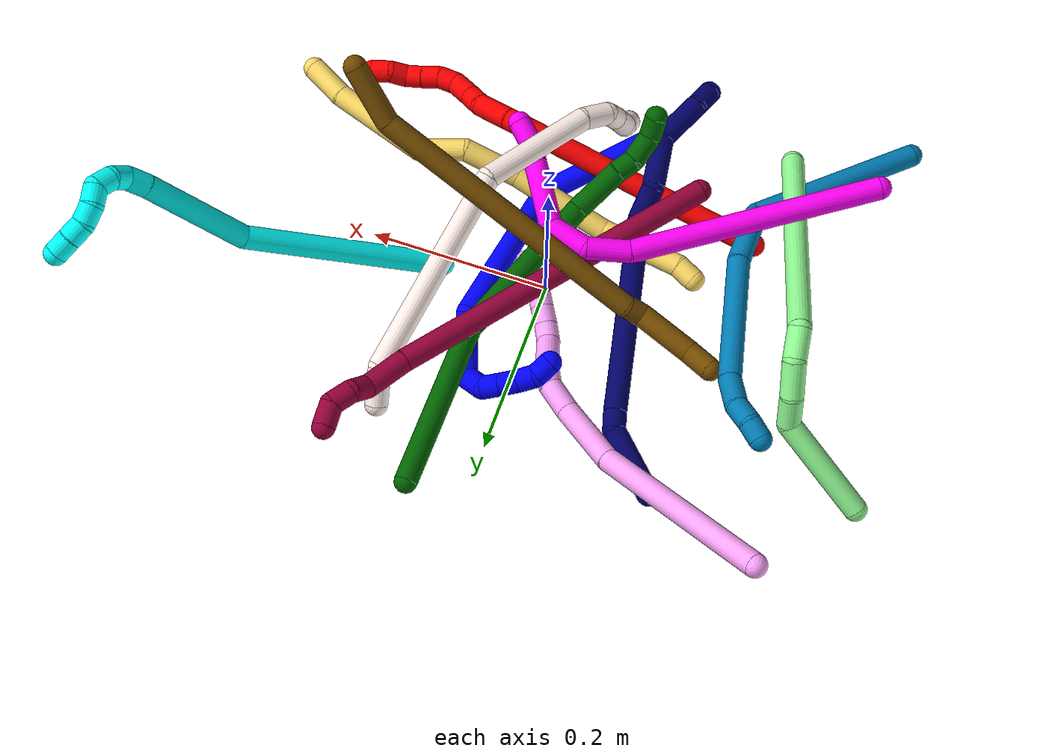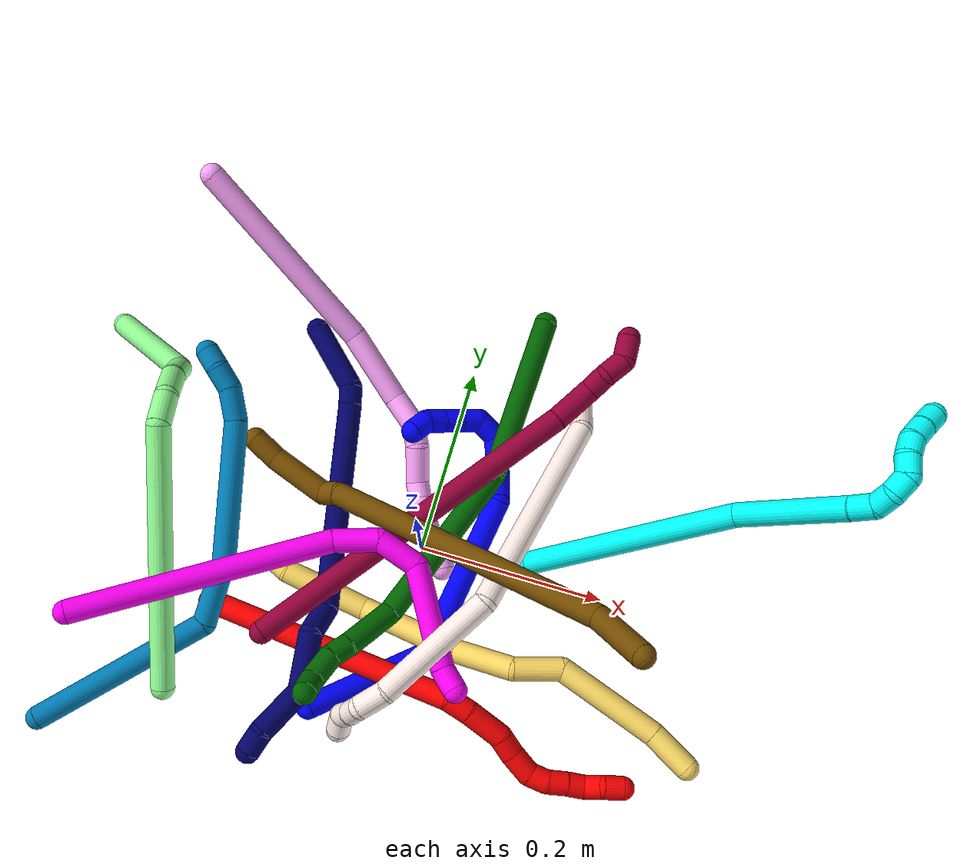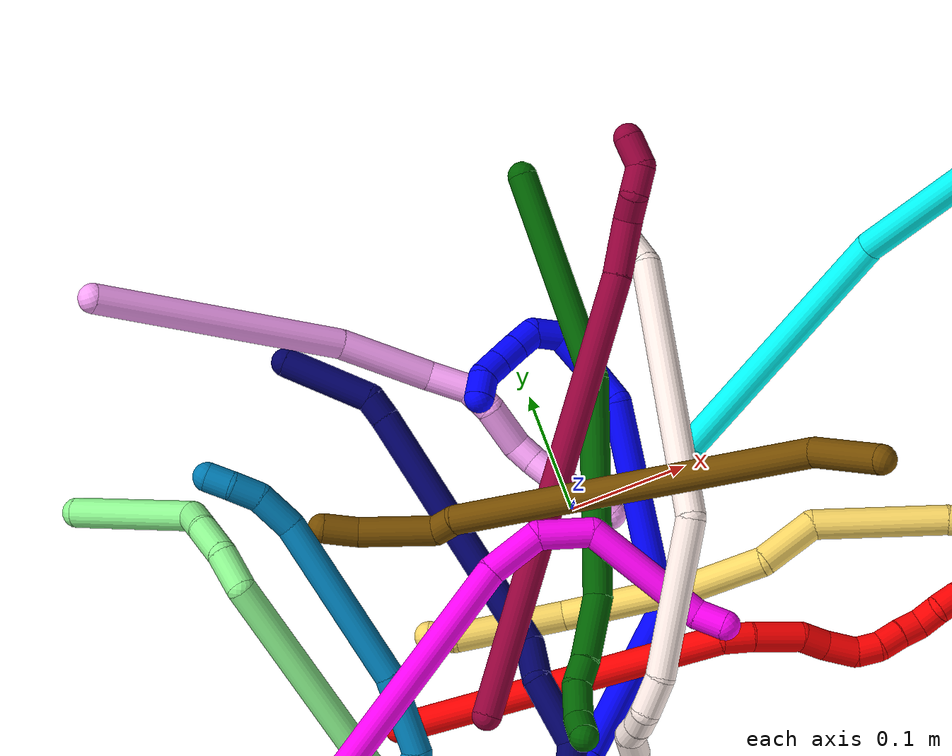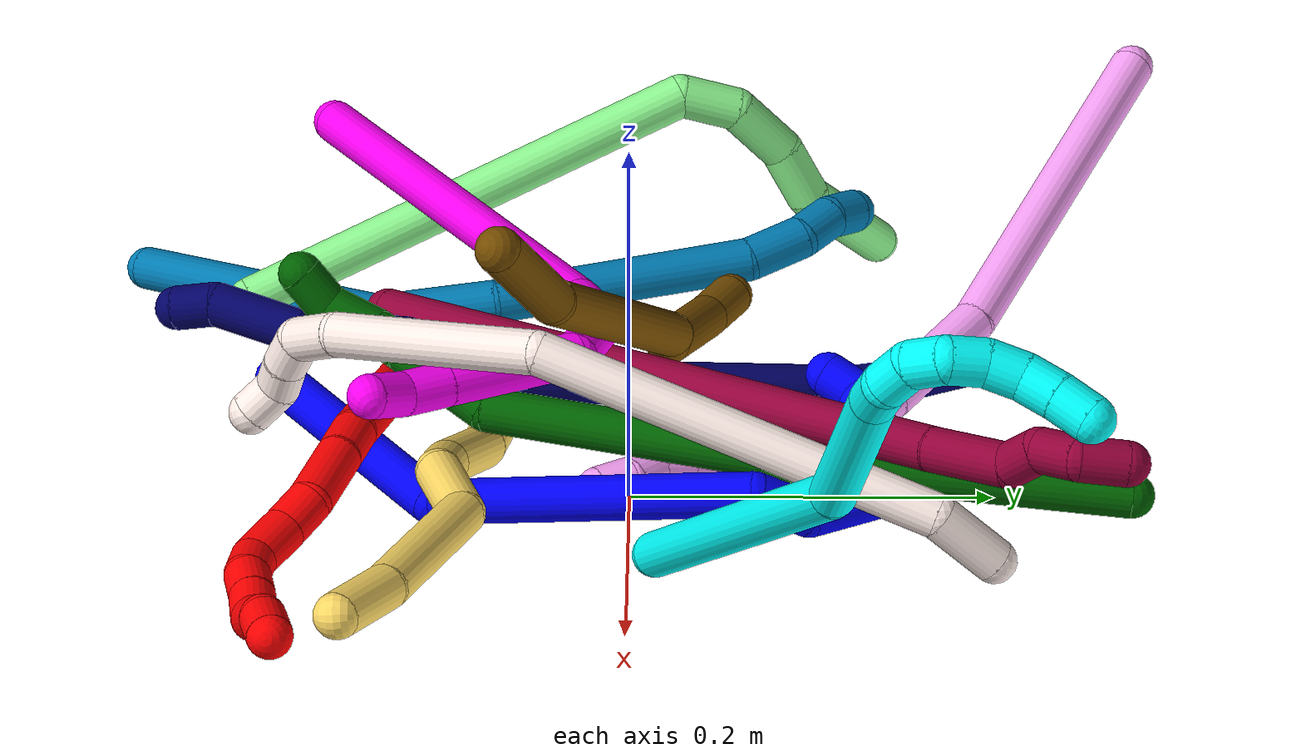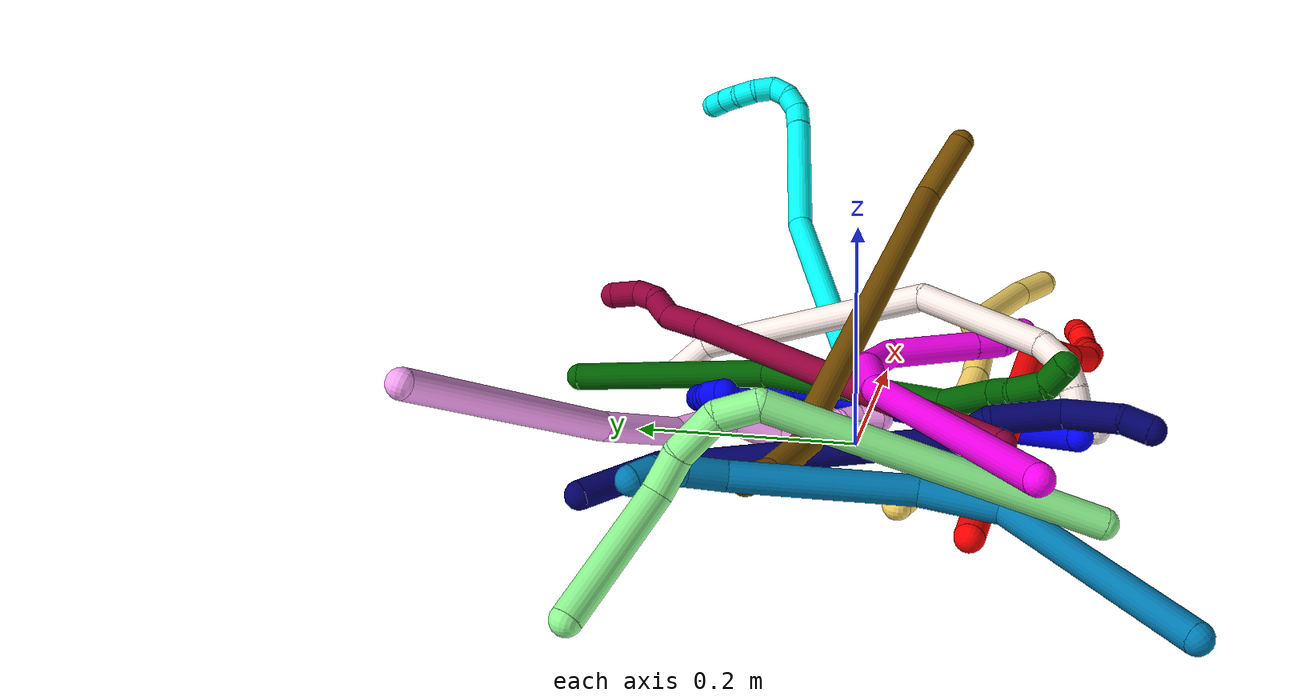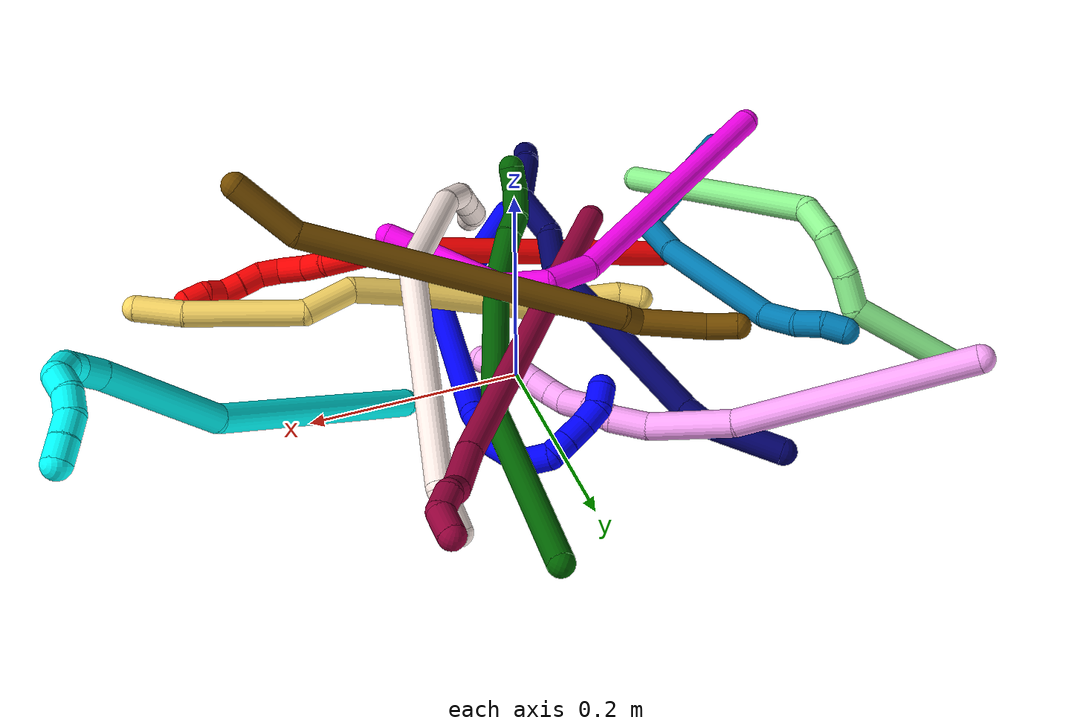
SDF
<sdf version="1.7">
 <world name="default">
  <plugin name="TubeGeneratorPlugin" filename="libtube_generator_plugin.so"/>
  <model name="photoneo_s_sensor">
   <static>1</static>
   <pose>0 0 2 1.57079 1.57079 3.14159</pose>
   <link name="link">
    <inertial><mass>0.1</mass></inertial>
    <sensor name="sensor" type="depth">
     <update_rate>30</update_rate>
     <camera>
      <horizontal_fov>1.22</horizontal_fov>
      <image><width>1920</width><height>1200</height><format>B8G8R8</format></image>
      <clip><near>0.1</near><far>4</far></clip>
      <depth_camera><output>points</output></depth_camera>
     </camera>
     <plugin name="camera_plugin" filename="libgazebo_ros_depth_camera.so">
      <baseline>0.2</baseline>
      <alwaysOn>1</alwaysOn>
      <updateRate>0.0</updateRate>
      <cameraName>camera_ir</cameraName>
      <imageTopicName>/camera/color/image_raw</imageTopicName>
      <cameraInfoTopicName>/camera/color/camera_info</cameraInfoTopicName>
      <depthImageTopicName>/camera/depth/image_raw</depthImageTopicName>
      <depthImageCameraInfoTopicName>/camera/depth/camera_info</depthImageCameraInfoTopicName>
      <pointCloudTopicName>/camera/depth/points</pointCloudTopicName>
      <frameName>fr_optical</frameName>
      <pointCloudCutoff>0.1</pointCloudCutoff>
      <pointCloudCutoffMax>2.0</pointCloudCutoffMax>
      <distortionK1>0</distortionK1>
      <distortionK2>0</distortionK2>
      <distortionK3>0</distortionK3>
      <distortionT1>0</distortionT1>
      <distortionT2>0</distortionT2>
      <CxPrime>0</CxPrime>
      <Cx>0</Cx>
      <Cy>0</Cy>
      <focalLength>0</focalLength>
      <hackBaseline>0</hackBaseline>
     </plugin>
    </sensor>
   </link>
  </model>
  <gravity>0 0 -9.8</gravity>
  <magnetic_field>6e-06 2.3e-05 -4.2e-05</magnetic_field>
  <atmosphere type="adiabatic"/>
  <physics name="default_physics" default="0" type="ode">
   <max_step_size>0.003</max_step_size>
   <real_time_factor>1</real_time_factor>
   <real_time_update_rate>1000</real_time_update_rate>
   <max_contacts>10000</max_contacts>
   <ode>
    <solver>
     <type>quick</type>
     <iters>100</iters>
     <sor>1.3</sor>
     <use_dynamic_moi_rescaling>0</use_dynamic_moi_rescaling>
    </solver>
    <constraints>
     <contact_max_correcting_vel>0</contact_max_correcting_vel>
     <contact_surface_layer>0.001</contact_surface_layer>
     <cfm>0</cfm>
     <erp>0.2</erp>
    </constraints>
   </ode>
  </physics>
  <scene><ambient>0.4 0.4 0.4 1</ambient><background>0.7 0.7 0.7 1</background><shadows>0</shadows></scene>
  <audio><device>default</device></audio>
  <spherical_coordinates>
   <surface_model>EARTH_WGS84</surface_model>
   <latitude_deg>0</latitude_deg>
   <longitude_deg>0</longitude_deg>
   <elevation>0</elevation>
   <heading_deg>0</heading_deg>
  </spherical_coordinates>
  <model name="bin">
   <static>1</static>
   <link name="bottom">
    <collision name="collision-bottom">
     <pose>0 0 -0.01 0 -0 0</pose>
     <geometry><box><size>0.8 0.6 0.02</size></box></geometry>
     <surface>
      <friction><ode><mu>100</mu><mu2>100</mu2></ode></friction>
      <contact><collide_bitmask>65535</collide_bitmask></contact>
     </surface>
    </collision>
   </link>
   <link name="west_wall">
    <collision name="collision-west_wall">
     <pose>-0.41 0 0.1 0 -0 0</pose>
     <geometry><box><size>0.02 0.6 0.2</size></box></geometry>
     <surface>
      <friction><ode><mu>100</mu><mu2>100</mu2></ode></friction>
      <contact><collide_bitmask>65535</collide_bitmask></contact>
     </surface>
    </collision>
   </link>
   <link name="east_wall">
    <collision name="collision-east_wall">
     <pose>0.41 0 0.1 0 -0 0</pose>
     <geometry><box><size>0.02 0.6 0.2</size></box></geometry>
     <surface>
      <friction><ode><mu>100</mu><mu2>100</mu2></ode></friction>
      <contact><collide_bitmask>65535</collide_bitmask></contact>
     </surface>
    </collision>
   </link>
   <link name="south_wall">
    <collision name="collision-south_wall">
     <pose>0 -0.31 0.1 0 -0 0</pose>
     <geometry><box><size>0.8 0.02 0.2</size></box></geometry>
     <surface>
      <friction><ode><mu>100</mu><mu2>100</mu2></ode></friction>
      <contact><collide_bitmask>65535</collide_bitmask></contact>
     </surface>
    </collision>
   </link>
   <link name="north_wall">
    <collision name="collision-north_wall">
     <pose>0 0.31 0.1 0 -0 0</pose>
     <geometry><box><size>0.8 0.02 0.2</size></box></geometry>
     <surface>
      <friction><ode><mu>100</mu><mu2>100</mu2></ode></friction>
      <contact><collide_bitmask>65535</collide_bitmask></contact>
     </surface>
    </collision>
   </link>
  </model>
  <model name="1">
   <static>0</static>
   <link name="1">
    <collision name="collision-cylinder-e_1_1_4">
     <pose>0.007021 0.038446 -0.056787 -2.54646 0.102026 -0.329949</pose>
     <geometry><cylinder><radius>0.0125</radius><length>0.137871</length></cylinder></geometry>
     <surface>
      <friction><ode><mu>1.16</mu><mu2>1.16</mu2><slip1>0</slip1><slip2>0</slip2></ode></friction>
      <contact><ode><kp>1e+06</kp><kd>1</kd><max_vel>0</max_vel><min_depth>0.001</min_depth></ode></contact>
     </surface>
    </collision>
    <visual name="visual-cylinder-e_1_1_4">
     <pose>0.007021 0.038446 -0.056787 -2.54646 0.102026 -0.329949</pose>
     <geometry><cylinder><radius>0.0125</radius><length>0.137871</length></cylinder></geometry>
     <material><ambient>0 0 1 1</ambient></material>
    </visual>
    <collision name="collision-cylinder-e_2_4_5">
     <pose>0.035803 0.161761 -0.131811 -1.78247 0.245619 -0.3032</pose>
     <geometry><cylinder><radius>0.0125</radius><length>0.178985</length></cylinder></geometry>
     <surface>
      <friction><ode><mu>1.16</mu><mu2>1.16</mu2><slip1>0</slip1><slip2>0</slip2></ode></friction>
      <contact><ode><kp>1e+06</kp><kd>1</kd><max_vel>0</max_vel><min_depth>0.001</min_depth></ode></contact>
     </surface>
    </collision>
    <visual name="visual-cylinder-e_2_4_5">
     <pose>0.035803 0.161761 -0.131811 -1.78247 0.245619 -0.3032</pose>
     <geometry><cylinder><radius>0.0125</radius><length>0.178985</length></cylinder></geometry>
     <material><ambient>0 0 1 1</ambient></material>
    </visual>
    <collision name="collision-cylinder-e_3_5_6">
     <pose>0.050543 0.262602 -0.150451 -1.59594 -0.414039 0.424275</pose>
     <geometry><cylinder><radius>0.0125</radius><length>0.034903</length></cylinder></geometry>
     <surface>
      <friction><ode><mu>1.16</mu><mu2>1.16</mu2><slip1>0</slip1><slip2>0</slip2></ode></friction>
      <contact><ode><kp>1e+06</kp><kd>1</kd><max_vel>0</max_vel><min_depth>0.001</min_depth></ode></contact>
     </surface>
    </collision>
    <visual name="visual-cylinder-e_3_5_6">
     <pose>0.050543 0.262602 -0.150451 -1.59594 -0.414039 0.424275</pose>
     <geometry><cylinder><radius>0.0125</radius><length>0.034903</length></cylinder></geometry>
     <material><ambient>0 0 1 1</ambient></material>
    </visual>
    <collision name="collision-cylinder-e_4_6_7">
     <pose>0.045719 0.298369 -0.145038 -1.28511 0.106073 -0.079431</pose>
     <geometry><cylinder><radius>0.0125</radius><length>0.041497</length></cylinder></geometry>
     <surface>
      <friction><ode><mu>1.16</mu><mu2>1.16</mu2><slip1>0</slip1><slip2>0</slip2></ode></friction>
      <contact><ode><kp>1e+06</kp><kd>1</kd><max_vel>0</max_vel><min_depth>0.001</min_depth></ode></contact>
     </surface>
    </collision>
    <visual name="visual-cylinder-e_4_6_7">
     <pose>0.045719 0.298369 -0.145038 -1.28511 0.106073 -0.079431</pose>
     <geometry><cylinder><radius>0.0125</radius><length>0.041497</length></cylinder></geometry>
     <material><ambient>0 0 1 1</ambient></material>
    </visual>
    <collision name="collision-cylinder-e_5_7_8">
     <pose>0.048677 0.324399 -0.128197 -0.514532 0.060035 -0.0158</pose>
     <geometry><cylinder><radius>0.0125</radius><length>0.02538</length></cylinder></geometry>
     <surface>
      <friction><ode><mu>1.16</mu><mu2>1.16</mu2><slip1>0</slip1><slip2>0</slip2></ode></friction>
      <contact><ode><kp>1e+06</kp><kd>1</kd><max_vel>0</max_vel><min_depth>0.001</min_depth></ode></contact>
     </surface>
    </collision>
    <visual name="visual-cylinder-e_5_7_8">
     <pose>0.048677 0.324399 -0.128197 -0.514532 0.060035 -0.0158</pose>
     <geometry><cylinder><radius>0.0125</radius><length>0.02538</length></cylinder></geometry>
     <material><ambient>0 0 1 1</ambient></material>
    </visual>
    <collision name="collision-cylinder-e_6_8_9">
     <pose>0.048938 0.328246 -0.107415 0.239973 -0.049736 -0.005998</pose>
     <geometry><cylinder><radius>0.0125</radius><length>0.020109</length></cylinder></geometry>
     <surface>
      <friction><ode><mu>1.16</mu><mu2>1.16</mu2><slip1>0</slip1><slip2>0</slip2></ode></friction>
      <contact><ode><kp>1e+06</kp><kd>1</kd><max_vel>0</max_vel><min_depth>0.001</min_depth></ode></contact>
     </surface>
    </collision>
    <visual name="visual-cylinder-e_6_8_9">
     <pose>0.048938 0.328246 -0.107415 0.239973 -0.049736 -0.005998</pose>
     <geometry><cylinder><radius>0.0125</radius><length>0.020109</length></cylinder></geometry>
     <material><ambient>0 0 1 1</ambient></material>
    </visual>
    <collision name="collision-cylinder-e_7_9_10">
     <pose>0.047911 0.323024 -0.087527 0.27279 -0.050065 -0.006873</pose>
     <geometry><cylinder><radius>0.0125</radius><length>0.021072</length></cylinder></geometry>
     <surface>
      <friction><ode><mu>1.16</mu><mu2>1.16</mu2><slip1>0</slip1><slip2>0</slip2></ode></friction>
      <contact><ode><kp>1e+06</kp><kd>1</kd><max_vel>0</max_vel><min_depth>0.001</min_depth></ode></contact>
     </surface>
    </collision>
    <visual name="visual-cylinder-e_7_9_10">
     <pose>0.047911 0.323024 -0.087527 0.27279 -0.050065 -0.006873</pose>
     <geometry><cylinder><radius>0.0125</radius><length>0.021072</length></cylinder></geometry>
     <material><ambient>0 0 1 1</ambient></material>
    </visual>
    <collision name="collision-cylinder-e_8_10_11">
     <pose>0.048265 0.317351 -0.06779 0.287287 0.087772 0.012703</pose>
     <geometry><cylinder><radius>0.0125</radius><length>0.020106</length></cylinder></geometry>
     <surface>
      <friction><ode><mu>1.16</mu><mu2>1.16</mu2><slip1>0</slip1><slip2>0</slip2></ode></friction>
      <contact><ode><kp>1e+06</kp><kd>1</kd><max_vel>0</max_vel><min_depth>0.001</min_depth></ode></contact>
     </surface>
    </collision>
    <visual name="visual-cylinder-e_8_10_11">
     <pose>0.048265 0.317351 -0.06779 0.287287 0.087772 0.012703</pose>
     <geometry><cylinder><radius>0.0125</radius><length>0.020106</length></cylinder></geometry>
     <material><ambient>0 0 1 1</ambient></material>
    </visual>
    <collision name="collision-cylinder-e_9_11_2">
     <pose>0.049776 0.307043 -0.051511 0.841617 0.062762 0.028096</pose>
     <geometry><cylinder><radius>0.0125</radius><length>0.020076</length></cylinder></geometry>
     <surface>
      <friction><ode><mu>1.16</mu><mu2>1.16</mu2><slip1>0</slip1><slip2>0</slip2></ode></friction>
      <contact><ode><kp>1e+06</kp><kd>1</kd><max_vel>0</max_vel><min_depth>0.001</min_depth></ode></contact>
     </surface>
    </collision>
    <visual name="visual-cylinder-e_9_11_2">
     <pose>0.049776 0.307043 -0.051511 0.841617 0.062762 0.028096</pose>
     <geometry><cylinder><radius>0.0125</radius><length>0.020076</length></cylinder></geometry>
     <material><ambient>0 0 1 1</ambient></material>
    </visual>
    <collision name="collision-sphere-2">
     <pose>0.050405 0.299572 -0.044836 0 -0 0</pose>
     <geometry><sphere><radius>0.0125</radius></sphere></geometry>
     <surface>
      <friction><ode><mu>1.16</mu><mu2>1.16</mu2><slip1>0</slip1><slip2>0</slip2></ode></friction>
      <contact><ode><kp>1e+06</kp><kd>1</kd><max_vel>0</max_vel><min_depth>0.001</min_depth></ode></contact>
     </surface>
    </collision>
    <visual name="visual-sphere-2">
     <pose>0.050405 0.299572 -0.044836 0 -0 0</pose>
     <geometry><sphere><radius>0.0125</radius></sphere></geometry>
     <material><ambient>0 0 1 1</ambient></material>
    </visual>
    <collision name="collision-sphere-11">
     <pose>0.049146 0.314514 -0.058185 0 -0 0</pose>
     <geometry><sphere><radius>0.0125</radius></sphere></geometry>
     <surface>
      <friction><ode><mu>1.16</mu><mu2>1.16</mu2><slip1>0</slip1><slip2>0</slip2></ode></friction>
      <contact><ode><kp>1e+06</kp><kd>1</kd><max_vel>0</max_vel><min_depth>0.001</min_depth></ode></contact>
     </surface>
    </collision>
    <visual name="visual-sphere-11">
     <pose>0.049146 0.314514 -0.058185 0 -0 0</pose>
     <geometry><sphere><radius>0.0125</radius></sphere></geometry>
     <material><ambient>0 0 1 1</ambient></material>
    </visual>
    <collision name="collision-sphere-10">
     <pose>0.047384 0.320189 -0.077394 0 -0 0</pose>
     <geometry><sphere><radius>0.0125</radius></sphere></geometry>
     <surface>
      <friction><ode><mu>1.16</mu><mu2>1.16</mu2><slip1>0</slip1><slip2>0</slip2></ode></friction>
      <contact><ode><kp>1e+06</kp><kd>1</kd><max_vel>0</max_vel><min_depth>0.001</min_depth></ode></contact>
     </surface>
    </collision>
    <visual name="visual-sphere-10">
     <pose>0.047384 0.320189 -0.077394 0 -0 0</pose>
     <geometry><sphere><radius>0.0125</radius></sphere></geometry>
     <material><ambient>0 0 1 1</ambient></material>
    </visual>
    <collision name="collision-sphere-9">
     <pose>0.048438 0.325859 -0.097661 0 -0 0</pose>
     <geometry><sphere><radius>0.0125</radius></sphere></geometry>
     <surface>
      <friction><ode><mu>1.16</mu><mu2>1.16</mu2><slip1>0</slip1><slip2>0</slip2></ode></friction>
      <contact><ode><kp>1e+06</kp><kd>1</kd><max_vel>0</max_vel><min_depth>0.001</min_depth></ode></contact>
     </surface>
    </collision>
    <visual name="visual-sphere-9">
     <pose>0.048438 0.325859 -0.097661 0 -0 0</pose>
     <geometry><sphere><radius>0.0125</radius></sphere></geometry>
     <material><ambient>0 0 1 1</ambient></material>
    </visual>
    <collision name="collision-sphere-4">
     <pose>0.014042 0.076892 -0.113574 0 -0 0</pose>
     <geometry><sphere><radius>0.0125</radius></sphere></geometry>
     <surface>
      <friction><ode><mu>1.16</mu><mu2>1.16</mu2><slip1>0</slip1><slip2>0</slip2></ode></friction>
      <contact><ode><kp>1e+06</kp><kd>1</kd><max_vel>0</max_vel><min_depth>0.001</min_depth></ode></contact>
     </surface>
    </collision>
    <visual name="visual-sphere-4">
     <pose>0.014042 0.076892 -0.113574 0 -0 0</pose>
     <geometry><sphere><radius>0.0125</radius></sphere></geometry>
     <material><ambient>0 0 1 1</ambient></material>
    </visual>
    <collision name="collision-sphere-1">
     <geometry><sphere><radius>0.0125</radius></sphere></geometry>
     <surface>
      <friction><ode><mu>1.16</mu><mu2>1.16</mu2><slip1>0</slip1><slip2>0</slip2></ode></friction>
      <contact><ode><kp>1e+06</kp><kd>1</kd><max_vel>0</max_vel><min_depth>0.001</min_depth></ode></contact>
     </surface>
    </collision>
    <visual name="visual-sphere-1">
     <geometry><sphere><radius>0.0125</radius></sphere></geometry>
     <material><ambient>0 0 1 1</ambient></material>
    </visual>
    <collision name="collision-sphere-8">
     <pose>0.049438 0.330633 -0.11717 0 -0 0</pose>
     <geometry><sphere><radius>0.0125</radius></sphere></geometry>
     <surface>
      <friction><ode><mu>1.16</mu><mu2>1.16</mu2><slip1>0</slip1><slip2>0</slip2></ode></friction>
      <contact><ode><kp>1e+06</kp><kd>1</kd><max_vel>0</max_vel><min_depth>0.001</min_depth></ode></contact>
     </surface>
    </collision>
    <visual name="visual-sphere-8">
     <pose>0.049438 0.330633 -0.11717 0 -0 0</pose>
     <geometry><sphere><radius>0.0125</radius></sphere></geometry>
     <material><ambient>0 0 1 1</ambient></material>
    </visual>
    <collision name="collision-sphere-5">
     <pose>0.057564 0.24663 -0.150049 0 -0 0</pose>
     <geometry><sphere><radius>0.0125</radius></sphere></geometry>
     <surface>
      <friction><ode><mu>1.16</mu><mu2>1.16</mu2><slip1>0</slip1><slip2>0</slip2></ode></friction>
      <contact><ode><kp>1e+06</kp><kd>1</kd><max_vel>0</max_vel><min_depth>0.001</min_depth></ode></contact>
     </surface>
    </collision>
    <visual name="visual-sphere-5">
     <pose>0.057564 0.24663 -0.150049 0 -0 0</pose>
     <geometry><sphere><radius>0.0125</radius></sphere></geometry>
     <material><ambient>0 0 1 1</ambient></material>
    </visual>
    <collision name="collision-sphere-6">
     <pose>0.043522 0.278574 -0.150852 0 -0 0</pose>
     <geometry><sphere><radius>0.0125</radius></sphere></geometry>
     <surface>
      <friction><ode><mu>1.16</mu><mu2>1.16</mu2><slip1>0</slip1><slip2>0</slip2></ode></friction>
      <contact><ode><kp>1e+06</kp><kd>1</kd><max_vel>0</max_vel><min_depth>0.001</min_depth></ode></contact>
     </surface>
    </collision>
    <visual name="visual-sphere-6">
     <pose>0.043522 0.278574 -0.150852 0 -0 0</pose>
     <geometry><sphere><radius>0.0125</radius></sphere></geometry>
     <material><ambient>0 0 1 1</ambient></material>
    </visual>
    <collision name="collision-sphere-7">
     <pose>0.047915 0.318165 -0.139224 0 -0 0</pose>
     <geometry><sphere><radius>0.0125</radius></sphere></geometry>
     <surface>
      <friction><ode><mu>1.16</mu><mu2>1.16</mu2><slip1>0</slip1><slip2>0</slip2></ode></friction>
      <contact><ode><kp>1e+06</kp><kd>1</kd><max_vel>0</max_vel><min_depth>0.001</min_depth></ode></contact>
     </surface>
    </collision>
    <visual name="visual-sphere-7">
     <pose>0.047915 0.318165 -0.139224 0 -0 0</pose>
     <geometry><sphere><radius>0.0125</radius></sphere></geometry>
     <material><ambient>0 0 1 1</ambient></material>
    </visual>
    <inertial>
     <pose>0.032473 0.179972 -0.104693 0 -0 0</pose>
     <mass>0.5</mass>
     <inertia>
      <ixx>0.000472</ixx>
      <ixy>0</ixy>
      <ixz>0</ixz>
      <iyy>-0.000412</iyy>
      <iyz>0</iyz>
      <izz>-0.000738</izz>
     </inertia>
    </inertial>
   </link>
   <pose>-0.061044 -0.196663 0.04571 -0.169611 -1.18303 0.291144</pose>
  </model>
  <model name="2">
   <static>0</static>
   <link name="2">
    <collision name="collision-cylinder-e_1_1_4">
     <pose>0.005912 0.002367 0.139723 -0.016939 0.042278 -0.000358</pose>
     <geometry><cylinder><radius>0.0125</radius><length>0.279735</length></cylinder></geometry>
     <surface>
      <friction><ode><mu>1.16</mu><mu2>1.16</mu2><slip1>0</slip1><slip2>0</slip2></ode></friction>
      <contact><ode><kp>1e+06</kp><kd>1</kd><max_vel>0</max_vel><min_depth>0.001</min_depth></ode></contact>
     </surface>
    </collision>
    <visual name="visual-cylinder-e_1_1_4">
     <pose>0.005912 0.002367 0.139723 -0.016939 0.042278 -0.000358</pose>
     <geometry><cylinder><radius>0.0125</radius><length>0.279735</length></cylinder></geometry>
     <material><ambient>1 0 0 1</ambient></material>
    </visual>
    <collision name="collision-cylinder-e_2_4_5">
     <pose>0.015129 0.000818 0.291206 0.321456 0.260605 0.042485</pose>
     <geometry><cylinder><radius>0.0125</radius><length>0.025657</length></cylinder></geometry>
     <surface>
      <friction><ode><mu>1.16</mu><mu2>1.16</mu2><slip1>0</slip1><slip2>0</slip2></ode></friction>
      <contact><ode><kp>1e+06</kp><kd>1</kd><max_vel>0</max_vel><min_depth>0.001</min_depth></ode></contact>
     </surface>
    </collision>
    <visual name="visual-cylinder-e_2_4_5">
     <pose>0.015129 0.000818 0.291206 0.321456 0.260605 0.042485</pose>
     <geometry><cylinder><radius>0.0125</radius><length>0.025657</length></cylinder></geometry>
     <material><ambient>1 0 0 1</ambient></material>
    </visual>
    <collision name="collision-cylinder-e_3_5_6">
     <pose>0.024793 -0.011688 0.321013 0.44421 0.308008 0.070084</pose>
     <geometry><cylinder><radius>0.0125</radius><length>0.041948</length></cylinder></geometry>
     <surface>
      <friction><ode><mu>1.16</mu><mu2>1.16</mu2><slip1>0</slip1><slip2>0</slip2></ode></friction>
      <contact><ode><kp>1e+06</kp><kd>1</kd><max_vel>0</max_vel><min_depth>0.001</min_depth></ode></contact>
     </surface>
    </collision>
    <visual name="visual-cylinder-e_3_5_6">
     <pose>0.024793 -0.011688 0.321013 0.44421 0.308008 0.070084</pose>
     <geometry><cylinder><radius>0.0125</radius><length>0.041948</length></cylinder></geometry>
     <material><ambient>1 0 0 1</ambient></material>
    </visual>
    <collision name="collision-cylinder-e_4_6_7">
     <pose>0.034208 -0.028264 0.346561 0.816785 0.272066 0.118322</pose>
     <geometry><cylinder><radius>0.0125</radius><length>0.02275</length></cylinder></geometry>
     <surface>
      <friction><ode><mu>1.16</mu><mu2>1.16</mu2><slip1>0</slip1><slip2>0</slip2></ode></friction>
      <contact><ode><kp>1e+06</kp><kd>1</kd><max_vel>0</max_vel><min_depth>0.001</min_depth></ode></contact>
     </surface>
    </collision>
    <visual name="visual-cylinder-e_4_6_7">
     <pose>0.034208 -0.028264 0.346561 0.816785 0.272066 0.118322</pose>
     <geometry><cylinder><radius>0.0125</radius><length>0.02275</length></cylinder></geometry>
     <material><ambient>1 0 0 1</ambient></material>
    </visual>
    <collision name="collision-cylinder-e_5_7_8">
     <pose>0.040058 -0.044677 0.365409 0.638722 0.195115 0.064704</pose>
     <geometry><cylinder><radius>0.0125</radius><length>0.028816</length></cylinder></geometry>
     <surface>
      <friction><ode><mu>1.16</mu><mu2>1.16</mu2><slip1>0</slip1><slip2>0</slip2></ode></friction>
      <contact><ode><kp>1e+06</kp><kd>1</kd><max_vel>0</max_vel><min_depth>0.001</min_depth></ode></contact>
     </surface>
    </collision>
    <visual name="visual-cylinder-e_5_7_8">
     <pose>0.040058 -0.044677 0.365409 0.638722 0.195115 0.064704</pose>
     <geometry><cylinder><radius>0.0125</radius><length>0.028816</length></cylinder></geometry>
     <material><ambient>1 0 0 1</ambient></material>
    </visual>
    <collision name="collision-cylinder-e_6_8_9">
     <pose>0.045404 -0.054377 0.386483 0.130204 0.254606 0.016689</pose>
     <geometry><cylinder><radius>0.0125</radius><length>0.020271</length></cylinder></geometry>
     <surface>
      <friction><ode><mu>1.16</mu><mu2>1.16</mu2><slip1>0</slip1><slip2>0</slip2></ode></friction>
      <contact><ode><kp>1e+06</kp><kd>1</kd><max_vel>0</max_vel><min_depth>0.001</min_depth></ode></contact>
     </surface>
    </collision>
    <visual name="visual-cylinder-e_6_8_9">
     <pose>0.045404 -0.054377 0.386483 0.130204 0.254606 0.016689</pose>
     <geometry><cylinder><radius>0.0125</radius><length>0.020271</length></cylinder></geometry>
     <material><ambient>1 0 0 1</ambient></material>
    </visual>
    <collision name="collision-cylinder-e_7_9_10">
     <pose>0.052974 -0.054838 0.405013 -0.092019 0.516129 -0.024304</pose>
     <geometry><cylinder><radius>0.0125</radius><length>0.020333</length></cylinder></geometry>
     <surface>
      <friction><ode><mu>1.16</mu><mu2>1.16</mu2><slip1>0</slip1><slip2>0</slip2></ode></friction>
      <contact><ode><kp>1e+06</kp><kd>1</kd><max_vel>0</max_vel><min_depth>0.001</min_depth></ode></contact>
     </surface>
    </collision>
    <visual name="visual-cylinder-e_7_9_10">
     <pose>0.052974 -0.054838 0.405013 -0.092019 0.516129 -0.024304</pose>
     <geometry><cylinder><radius>0.0125</radius><length>0.020333</length></cylinder></geometry>
     <material><ambient>1 0 0 1</ambient></material>
    </visual>
    <collision name="collision-cylinder-e_8_10_11">
     <pose>0.062901 -0.054158 0.42261 0.015084 0.509243 0.003926</pose>
     <geometry><cylinder><radius>0.0125</radius><length>0.020142</length></cylinder></geometry>
     <surface>
      <friction><ode><mu>1.16</mu><mu2>1.16</mu2><slip1>0</slip1><slip2>0</slip2></ode></friction>
      <contact><ode><kp>1e+06</kp><kd>1</kd><max_vel>0</max_vel><min_depth>0.001</min_depth></ode></contact>
     </surface>
    </collision>
    <visual name="visual-cylinder-e_8_10_11">
     <pose>0.062901 -0.054158 0.42261 0.015084 0.509243 0.003926</pose>
     <geometry><cylinder><radius>0.0125</radius><length>0.020142</length></cylinder></geometry>
     <material><ambient>1 0 0 1</ambient></material>
    </visual>
    <collision name="collision-cylinder-e_9_11_12">
     <pose>0.068097 -0.049895 0.440442 -0.452663 0.028474 -0.006557</pose>
     <geometry><cylinder><radius>0.0125</radius><length>0.020112</length></cylinder></geometry>
     <surface>
      <friction><ode><mu>1.16</mu><mu2>1.16</mu2><slip1>0</slip1><slip2>0</slip2></ode></friction>
      <contact><ode><kp>1e+06</kp><kd>1</kd><max_vel>0</max_vel><min_depth>0.001</min_depth></ode></contact>
     </surface>
    </collision>
    <visual name="visual-cylinder-e_9_11_12">
     <pose>0.068097 -0.049895 0.440442 -0.452663 0.028474 -0.006557</pose>
     <geometry><cylinder><radius>0.0125</radius><length>0.020112</length></cylinder></geometry>
     <material><ambient>1 0 0 1</ambient></material>
    </visual>
    <collision name="collision-cylinder-e_10_12_2">
     <pose>0.072939 -0.043949 0.458382 -0.172319 0.467061 -0.041085</pose>
     <geometry><cylinder><radius>0.0125</radius><length>0.020236</length></cylinder></geometry>
     <surface>
      <friction><ode><mu>1.16</mu><mu2>1.16</mu2><slip1>0</slip1><slip2>0</slip2></ode></friction>
      <contact><ode><kp>1e+06</kp><kd>1</kd><max_vel>0</max_vel><min_depth>0.001</min_depth></ode></contact>
     </surface>
    </collision>
    <visual name="visual-cylinder-e_10_12_2">
     <pose>0.072939 -0.043949 0.458382 -0.172319 0.467061 -0.041085</pose>
     <geometry><cylinder><radius>0.0125</radius><length>0.020236</length></cylinder></geometry>
     <material><ambient>1 0 0 1</ambient></material>
    </visual>
    <collision name="collision-sphere-2">
     <pose>0.077495 -0.0424 0.467283 0 -0 0</pose>
     <geometry><sphere><radius>0.0125</radius></sphere></geometry>
     <surface>
      <friction><ode><mu>1.16</mu><mu2>1.16</mu2><slip1>0</slip1><slip2>0</slip2></ode></friction>
      <contact><ode><kp>1e+06</kp><kd>1</kd><max_vel>0</max_vel><min_depth>0.001</min_depth></ode></contact>
     </surface>
    </collision>
    <visual name="visual-sphere-2">
     <pose>0.077495 -0.0424 0.467283 0 -0 0</pose>
     <geometry><sphere><radius>0.0125</radius></sphere></geometry>
     <material><ambient>1 0 0 1</ambient></material>
    </visual>
    <collision name="collision-sphere-12">
     <pose>0.068384 -0.045498 0.449482 0 -0 0</pose>
     <geometry><sphere><radius>0.0125</radius></sphere></geometry>
     <surface>
      <friction><ode><mu>1.16</mu><mu2>1.16</mu2><slip1>0</slip1><slip2>0</slip2></ode></friction>
      <contact><ode><kp>1e+06</kp><kd>1</kd><max_vel>0</max_vel><min_depth>0.001</min_depth></ode></contact>
     </surface>
    </collision>
    <visual name="visual-sphere-12">
     <pose>0.068384 -0.045498 0.449482 0 -0 0</pose>
     <geometry><sphere><radius>0.0125</radius></sphere></geometry>
     <material><ambient>1 0 0 1</ambient></material>
    </visual>
    <collision name="collision-sphere-11">
     <pose>0.067811 -0.054291 0.431403 0 -0 0</pose>
     <geometry><sphere><radius>0.0125</radius></sphere></geometry>
     <surface>
      <friction><ode><mu>1.16</mu><mu2>1.16</mu2><slip1>0</slip1><slip2>0</slip2></ode></friction>
      <contact><ode><kp>1e+06</kp><kd>1</kd><max_vel>0</max_vel><min_depth>0.001</min_depth></ode></contact>
     </surface>
    </collision>
    <visual name="visual-sphere-11">
     <pose>0.067811 -0.054291 0.431403 0 -0 0</pose>
     <geometry><sphere><radius>0.0125</radius></sphere></geometry>
     <material><ambient>1 0 0 1</ambient></material>
    </visual>
    <collision name="collision-sphere-10">
     <pose>0.057991 -0.054026 0.413818 0 -0 0</pose>
     <geometry><sphere><radius>0.0125</radius></sphere></geometry>
     <surface>
      <friction><ode><mu>1.16</mu><mu2>1.16</mu2><slip1>0</slip1><slip2>0</slip2></ode></friction>
      <contact><ode><kp>1e+06</kp><kd>1</kd><max_vel>0</max_vel><min_depth>0.001</min_depth></ode></contact>
     </surface>
    </collision>
    <visual name="visual-sphere-10">
     <pose>0.057991 -0.054026 0.413818 0 -0 0</pose>
     <geometry><sphere><radius>0.0125</radius></sphere></geometry>
     <material><ambient>1 0 0 1</ambient></material>
    </visual>
    <collision name="collision-sphere-9">
     <pose>0.047957 -0.055651 0.396209 0 -0 0</pose>
     <geometry><sphere><radius>0.0125</radius></sphere></geometry>
     <surface>
      <friction><ode><mu>1.16</mu><mu2>1.16</mu2><slip1>0</slip1><slip2>0</slip2></ode></friction>
      <contact><ode><kp>1e+06</kp><kd>1</kd><max_vel>0</max_vel><min_depth>0.001</min_depth></ode></contact>
     </surface>
    </collision>
    <visual name="visual-sphere-9">
     <pose>0.047957 -0.055651 0.396209 0 -0 0</pose>
     <geometry><sphere><radius>0.0125</radius></sphere></geometry>
     <material><ambient>1 0 0 1</ambient></material>
    </visual>
    <collision name="collision-sphere-4">
     <pose>0.011823 0.004734 0.279445 0 -0 0</pose>
     <geometry><sphere><radius>0.0125</radius></sphere></geometry>
     <surface>
      <friction><ode><mu>1.16</mu><mu2>1.16</mu2><slip1>0</slip1><slip2>0</slip2></ode></friction>
      <contact><ode><kp>1e+06</kp><kd>1</kd><max_vel>0</max_vel><min_depth>0.001</min_depth></ode></contact>
     </surface>
    </collision>
    <visual name="visual-sphere-4">
     <pose>0.011823 0.004734 0.279445 0 -0 0</pose>
     <geometry><sphere><radius>0.0125</radius></sphere></geometry>
     <material><ambient>1 0 0 1</ambient></material>
    </visual>
    <collision name="collision-sphere-1">
     <geometry><sphere><radius>0.0125</radius></sphere></geometry>
     <surface>
      <friction><ode><mu>1.16</mu><mu2>1.16</mu2><slip1>0</slip1><slip2>0</slip2></ode></friction>
      <contact><ode><kp>1e+06</kp><kd>1</kd><max_vel>0</max_vel><min_depth>0.001</min_depth></ode></contact>
     </surface>
    </collision>
    <visual name="visual-sphere-1">
     <geometry><sphere><radius>0.0125</radius></sphere></geometry>
     <material><ambient>1 0 0 1</ambient></material>
    </visual>
    <collision name="collision-sphere-8">
     <pose>0.042851 -0.053104 0.376757 0 -0 0</pose>
     <geometry><sphere><radius>0.0125</radius></sphere></geometry>
     <surface>
      <friction><ode><mu>1.16</mu><mu2>1.16</mu2><slip1>0</slip1><slip2>0</slip2></ode></friction>
      <contact><ode><kp>1e+06</kp><kd>1</kd><max_vel>0</max_vel><min_depth>0.001</min_depth></ode></contact>
     </surface>
    </collision>
    <visual name="visual-sphere-8">
     <pose>0.042851 -0.053104 0.376757 0 -0 0</pose>
     <geometry><sphere><radius>0.0125</radius></sphere></geometry>
     <material><ambient>1 0 0 1</ambient></material>
    </visual>
    <collision name="collision-sphere-5">
     <pose>0.018434 -0.003099 0.302966 0 -0 0</pose>
     <geometry><sphere><radius>0.0125</radius></sphere></geometry>
     <surface>
      <friction><ode><mu>1.16</mu><mu2>1.16</mu2><slip1>0</slip1><slip2>0</slip2></ode></friction>
      <contact><ode><kp>1e+06</kp><kd>1</kd><max_vel>0</max_vel><min_depth>0.001</min_depth></ode></contact>
     </surface>
    </collision>
    <visual name="visual-sphere-5">
     <pose>0.018434 -0.003099 0.302966 0 -0 0</pose>
     <geometry><sphere><radius>0.0125</radius></sphere></geometry>
     <material><ambient>1 0 0 1</ambient></material>
    </visual>
    <collision name="collision-sphere-6">
     <pose>0.031151 -0.020277 0.33906 0 -0 0</pose>
     <geometry><sphere><radius>0.0125</radius></sphere></geometry>
     <surface>
      <friction><ode><mu>1.16</mu><mu2>1.16</mu2><slip1>0</slip1><slip2>0</slip2></ode></friction>
      <contact><ode><kp>1e+06</kp><kd>1</kd><max_vel>0</max_vel><min_depth>0.001</min_depth></ode></contact>
     </surface>
    </collision>
    <visual name="visual-sphere-6">
     <pose>0.031151 -0.020277 0.33906 0 -0 0</pose>
     <geometry><sphere><radius>0.0125</radius></sphere></geometry>
     <material><ambient>1 0 0 1</ambient></material>
    </visual>
    <collision name="collision-sphere-7">
     <pose>0.037264 -0.036251 0.354061 0 -0 0</pose>
     <geometry><sphere><radius>0.0125</radius></sphere></geometry>
     <surface>
      <friction><ode><mu>1.16</mu><mu2>1.16</mu2><slip1>0</slip1><slip2>0</slip2></ode></friction>
      <contact><ode><kp>1e+06</kp><kd>1</kd><max_vel>0</max_vel><min_depth>0.001</min_depth></ode></contact>
     </surface>
    </collision>
    <visual name="visual-sphere-7">
     <pose>0.037264 -0.036251 0.354061 0 -0 0</pose>
     <geometry><sphere><radius>0.0125</radius></sphere></geometry>
     <material><ambient>1 0 0 1</ambient></material>
    </visual>
    <inertial>
     <pose>0.022249 -0.013877 0.242305 0 -0 0</pose>
     <mass>0.5</mass>
     <inertia>
      <ixx>0.001861</ixx>
      <ixy>0</ixy>
      <ixz>0</ixz>
      <iyy>0.001852</iyy>
      <iyz>0</iyz>
      <izz>-7.2e-05</izz>
     </inertia>
    </inertial>
   </link>
   <pose>-0.199398 -0.120251 0.011499 1.14497 1.00254 1.06858</pose>
  </model>
  <model name="3">
   <static>0</static>
   <link name="3">
    <collision name="collision-cylinder-e_1_1_4">
     <pose>0.008518 0.000524 0.115912 -0.004522 0.073352 -0.000166</pose>
     <geometry><cylinder><radius>0.0125</radius><length>0.232451</length></cylinder></geometry>
     <surface>
      <friction><ode><mu>1.16</mu><mu2>1.16</mu2><slip1>0</slip1><slip2>0</slip2></ode></friction>
      <contact><ode><kp>1e+06</kp><kd>1</kd><max_vel>0</max_vel><min_depth>0.001</min_depth></ode></contact>
     </surface>
    </collision>
    <visual name="visual-cylinder-e_1_1_4">
     <pose>0.008518 0.000524 0.115912 -0.004522 0.073352 -0.000166</pose>
     <geometry><cylinder><radius>0.0125</radius><length>0.232451</length></cylinder></geometry>
     <material><ambient>0.003922 1 0.996078 1</ambient></material>
    </visual>
    <collision name="collision-cylinder-e_2_4_5">
     <pose>0.000416 0.002 0.291247 -0.016005 -0.272669 0.002196</pose>
     <geometry><cylinder><radius>0.0125</radius><length>0.123423</length></cylinder></geometry>
     <surface>
      <friction><ode><mu>1.16</mu><mu2>1.16</mu2><slip1>0</slip1><slip2>0</slip2></ode></friction>
      <contact><ode><kp>1e+06</kp><kd>1</kd><max_vel>0</max_vel><min_depth>0.001</min_depth></ode></contact>
     </surface>
    </collision>
    <visual name="visual-cylinder-e_2_4_5">
     <pose>0.000416 0.002 0.291247 -0.016005 -0.272669 0.002196</pose>
     <geometry><cylinder><radius>0.0125</radius><length>0.123423</length></cylinder></geometry>
     <material><ambient>0.003922 1 0.996078 1</ambient></material>
    </visual>
    <collision name="collision-cylinder-e_3_5_6">
     <pose>-0.018284 0.002938 0.362541 0.001063 -0.173564 -9.2e-05</pose>
     <geometry><cylinder><radius>0.0125</radius><length>0.024102</length></cylinder></geometry>
     <surface>
      <friction><ode><mu>1.16</mu><mu2>1.16</mu2><slip1>0</slip1><slip2>0</slip2></ode></friction>
      <contact><ode><kp>1e+06</kp><kd>1</kd><max_vel>0</max_vel><min_depth>0.001</min_depth></ode></contact>
     </surface>
    </collision>
    <visual name="visual-cylinder-e_3_5_6">
     <pose>-0.018284 0.002938 0.362541 0.001063 -0.173564 -9.2e-05</pose>
     <geometry><cylinder><radius>0.0125</radius><length>0.024102</length></cylinder></geometry>
     <material><ambient>0.003922 1 0.996078 1</ambient></material>
    </visual>
    <collision name="collision-cylinder-e_4_6_7">
     <pose>-0.020284 0.007702 0.383199 -0.497797 0.008084 -0.002055</pose>
     <geometry><cylinder><radius>0.0125</radius><length>0.020005</length></cylinder></geometry>
     <surface>
      <friction><ode><mu>1.16</mu><mu2>1.16</mu2><slip1>0</slip1><slip2>0</slip2></ode></friction>
      <contact><ode><kp>1e+06</kp><kd>1</kd><max_vel>0</max_vel><min_depth>0.001</min_depth></ode></contact>
     </surface>
    </collision>
    <visual name="visual-cylinder-e_4_6_7">
     <pose>-0.020284 0.007702 0.383199 -0.497797 0.008084 -0.002055</pose>
     <geometry><cylinder><radius>0.0125</radius><length>0.020005</length></cylinder></geometry>
     <material><ambient>0.003922 1 0.996078 1</ambient></material>
    </visual>
    <collision name="collision-cylinder-e_5_7_8">
     <pose>-0.015485 0.01684 0.399657 -0.517159 0.49105 -0.132364</pose>
     <geometry><cylinder><radius>0.0125</radius><length>0.020012</length></cylinder></geometry>
     <surface>
      <friction><ode><mu>1.16</mu><mu2>1.16</mu2><slip1>0</slip1><slip2>0</slip2></ode></friction>
      <contact><ode><kp>1e+06</kp><kd>1</kd><max_vel>0</max_vel><min_depth>0.001</min_depth></ode></contact>
     </surface>
    </collision>
    <visual name="visual-cylinder-e_5_7_8">
     <pose>-0.015485 0.01684 0.399657 -0.517159 0.49105 -0.132364</pose>
     <geometry><cylinder><radius>0.0125</radius><length>0.020012</length></cylinder></geometry>
     <material><ambient>0.003922 1 0.996078 1</ambient></material>
    </visual>
    <collision name="collision-cylinder-e_6_8_9">
     <pose>-0.003222 0.027683 0.408403 -1.40618 0.85442 -0.73652</pose>
     <geometry><cylinder><radius>0.0125</radius><length>0.020008</length></cylinder></geometry>
     <surface>
      <friction><ode><mu>1.16</mu><mu2>1.16</mu2><slip1>0</slip1><slip2>0</slip2></ode></friction>
      <contact><ode><kp>1e+06</kp><kd>1</kd><max_vel>0</max_vel><min_depth>0.001</min_depth></ode></contact>
     </surface>
    </collision>
    <visual name="visual-cylinder-e_6_8_9">
     <pose>-0.003222 0.027683 0.408403 -1.40618 0.85442 -0.73652</pose>
     <geometry><cylinder><radius>0.0125</radius><length>0.020008</length></cylinder></geometry>
     <material><ambient>0.003922 1 0.996078 1</ambient></material>
    </visual>
    <collision name="collision-cylinder-e_7_9_10">
     <pose>0.013371 0.037754 0.411771 -1.00273 1.13076 -0.669314</pose>
     <geometry><cylinder><radius>0.0125</radius><length>0.02</length></cylinder></geometry>
     <surface>
      <friction><ode><mu>1.16</mu><mu2>1.16</mu2><slip1>0</slip1><slip2>0</slip2></ode></friction>
      <contact><ode><kp>1e+06</kp><kd>1</kd><max_vel>0</max_vel><min_depth>0.001</min_depth></ode></contact>
     </surface>
    </collision>
    <visual name="visual-cylinder-e_7_9_10">
     <pose>0.013371 0.037754 0.411771 -1.00273 1.13076 -0.669314</pose>
     <geometry><cylinder><radius>0.0125</radius><length>0.02</length></cylinder></geometry>
     <material><ambient>0.003922 1 0.996078 1</ambient></material>
    </visual>
    <collision name="collision-cylinder-e_8_10_11">
     <pose>0.031335 0.042156 0.418516 -0.180344 1.10112 -0.110896</pose>
     <geometry><cylinder><radius>0.0125</radius><length>0.02</length></cylinder></geometry>
     <surface>
      <friction><ode><mu>1.16</mu><mu2>1.16</mu2><slip1>0</slip1><slip2>0</slip2></ode></friction>
      <contact><ode><kp>1e+06</kp><kd>1</kd><max_vel>0</max_vel><min_depth>0.001</min_depth></ode></contact>
     </surface>
    </collision>
    <visual name="visual-cylinder-e_8_10_11">
     <pose>0.031335 0.042156 0.418516 -0.180344 1.10112 -0.110896</pose>
     <geometry><cylinder><radius>0.0125</radius><length>0.02</length></cylinder></geometry>
     <material><ambient>0.003922 1 0.996078 1</ambient></material>
    </visual>
    <collision name="collision-cylinder-e_9_11_2">
     <pose>0.049357 0.04309 0.427103 -0.029415 1.14433 -0.018945</pose>
     <geometry><cylinder><radius>0.0125</radius><length>0.02</length></cylinder></geometry>
     <surface>
      <friction><ode><mu>1.16</mu><mu2>1.16</mu2><slip1>0</slip1><slip2>0</slip2></ode></friction>
      <contact><ode><kp>1e+06</kp><kd>1</kd><max_vel>0</max_vel><min_depth>0.001</min_depth></ode></contact>
     </surface>
    </collision>
    <visual name="visual-cylinder-e_9_11_2">
     <pose>0.049357 0.04309 0.427103 -0.029415 1.14433 -0.018945</pose>
     <geometry><cylinder><radius>0.0125</radius><length>0.02</length></cylinder></geometry>
     <material><ambient>0.003922 1 0.996078 1</ambient></material>
    </visual>
    <collision name="collision-sphere-2">
     <pose>0.058461 0.043211 0.431238 0 -0 0</pose>
     <geometry><sphere><radius>0.0125</radius></sphere></geometry>
     <surface>
      <friction><ode><mu>1.16</mu><mu2>1.16</mu2><slip1>0</slip1><slip2>0</slip2></ode></friction>
      <contact><ode><kp>1e+06</kp><kd>1</kd><max_vel>0</max_vel><min_depth>0.001</min_depth></ode></contact>
     </surface>
    </collision>
    <visual name="visual-sphere-2">
     <pose>0.058461 0.043211 0.431238 0 -0 0</pose>
     <geometry><sphere><radius>0.0125</radius></sphere></geometry>
     <material><ambient>0.003922 1 0.996078 1</ambient></material>
    </visual>
    <collision name="collision-sphere-11">
     <pose>0.040252 0.042968 0.422968 0 -0 0</pose>
     <geometry><sphere><radius>0.0125</radius></sphere></geometry>
     <surface>
      <friction><ode><mu>1.16</mu><mu2>1.16</mu2><slip1>0</slip1><slip2>0</slip2></ode></friction>
      <contact><ode><kp>1e+06</kp><kd>1</kd><max_vel>0</max_vel><min_depth>0.001</min_depth></ode></contact>
     </surface>
    </collision>
    <visual name="visual-sphere-11">
     <pose>0.040252 0.042968 0.422968 0 -0 0</pose>
     <geometry><sphere><radius>0.0125</radius></sphere></geometry>
     <material><ambient>0.003922 1 0.996078 1</ambient></material>
    </visual>
    <collision name="collision-sphere-10">
     <pose>0.022418 0.041344 0.414063 0 -0 0</pose>
     <geometry><sphere><radius>0.0125</radius></sphere></geometry>
     <surface>
      <friction><ode><mu>1.16</mu><mu2>1.16</mu2><slip1>0</slip1><slip2>0</slip2></ode></friction>
      <contact><ode><kp>1e+06</kp><kd>1</kd><max_vel>0</max_vel><min_depth>0.001</min_depth></ode></contact>
     </surface>
    </collision>
    <visual name="visual-sphere-10">
     <pose>0.022418 0.041344 0.414063 0 -0 0</pose>
     <geometry><sphere><radius>0.0125</radius></sphere></geometry>
     <material><ambient>0.003922 1 0.996078 1</ambient></material>
    </visual>
    <collision name="collision-sphere-9">
     <pose>0.004323 0.034163 0.40948 0 -0 0</pose>
     <geometry><sphere><radius>0.0125</radius></sphere></geometry>
     <surface>
      <friction><ode><mu>1.16</mu><mu2>1.16</mu2><slip1>0</slip1><slip2>0</slip2></ode></friction>
      <contact><ode><kp>1e+06</kp><kd>1</kd><max_vel>0</max_vel><min_depth>0.001</min_depth></ode></contact>
     </surface>
    </collision>
    <visual name="visual-sphere-9">
     <pose>0.004323 0.034163 0.40948 0 -0 0</pose>
     <geometry><sphere><radius>0.0125</radius></sphere></geometry>
     <material><ambient>0.003922 1 0.996078 1</ambient></material>
    </visual>
    <collision name="collision-sphere-4">
     <pose>0.017035 0.001048 0.231823 0 -0 0</pose>
     <geometry><sphere><radius>0.0125</radius></sphere></geometry>
     <surface>
      <friction><ode><mu>1.16</mu><mu2>1.16</mu2><slip1>0</slip1><slip2>0</slip2></ode></friction>
      <contact><ode><kp>1e+06</kp><kd>1</kd><max_vel>0</max_vel><min_depth>0.001</min_depth></ode></contact>
     </surface>
    </collision>
    <visual name="visual-sphere-4">
     <pose>0.017035 0.001048 0.231823 0 -0 0</pose>
     <geometry><sphere><radius>0.0125</radius></sphere></geometry>
     <material><ambient>0.003922 1 0.996078 1</ambient></material>
    </visual>
    <collision name="collision-sphere-1">
     <geometry><sphere><radius>0.0125</radius></sphere></geometry>
     <surface>
      <friction><ode><mu>1.16</mu><mu2>1.16</mu2><slip1>0</slip1><slip2>0</slip2></ode></friction>
      <contact><ode><kp>1e+06</kp><kd>1</kd><max_vel>0</max_vel><min_depth>0.001</min_depth></ode></contact>
     </surface>
    </collision>
    <visual name="visual-sphere-1">
     <geometry><sphere><radius>0.0125</radius></sphere></geometry>
     <material><ambient>0.003922 1 0.996078 1</ambient></material>
    </visual>
    <collision name="collision-sphere-8">
     <pose>-0.010766 0.021203 0.407327 0 -0 0</pose>
     <geometry><sphere><radius>0.0125</radius></sphere></geometry>
     <surface>
      <friction><ode><mu>1.16</mu><mu2>1.16</mu2><slip1>0</slip1><slip2>0</slip2></ode></friction>
      <contact><ode><kp>1e+06</kp><kd>1</kd><max_vel>0</max_vel><min_depth>0.001</min_depth></ode></contact>
     </surface>
    </collision>
    <visual name="visual-sphere-8">
     <pose>-0.010766 0.021203 0.407327 0 -0 0</pose>
     <geometry><sphere><radius>0.0125</radius></sphere></geometry>
     <material><ambient>0.003922 1 0.996078 1</ambient></material>
    </visual>
    <collision name="collision-sphere-5">
     <pose>-0.016203 0.002951 0.350671 0 -0 0</pose>
     <geometry><sphere><radius>0.0125</radius></sphere></geometry>
     <surface>
      <friction><ode><mu>1.16</mu><mu2>1.16</mu2><slip1>0</slip1><slip2>0</slip2></ode></friction>
      <contact><ode><kp>1e+06</kp><kd>1</kd><max_vel>0</max_vel><min_depth>0.001</min_depth></ode></contact>
     </surface>
    </collision>
    <visual name="visual-sphere-5">
     <pose>-0.016203 0.002951 0.350671 0 -0 0</pose>
     <geometry><sphere><radius>0.0125</radius></sphere></geometry>
     <material><ambient>0.003922 1 0.996078 1</ambient></material>
    </visual>
    <collision name="collision-sphere-6">
     <pose>-0.020365 0.002925 0.37441 0 -0 0</pose>
     <geometry><sphere><radius>0.0125</radius></sphere></geometry>
     <surface>
      <friction><ode><mu>1.16</mu><mu2>1.16</mu2><slip1>0</slip1><slip2>0</slip2></ode></friction>
      <contact><ode><kp>1e+06</kp><kd>1</kd><max_vel>0</max_vel><min_depth>0.001</min_depth></ode></contact>
     </surface>
    </collision>
    <visual name="visual-sphere-6">
     <pose>-0.020365 0.002925 0.37441 0 -0 0</pose>
     <geometry><sphere><radius>0.0125</radius></sphere></geometry>
     <material><ambient>0.003922 1 0.996078 1</ambient></material>
    </visual>
    <collision name="collision-sphere-7">
     <pose>-0.020203 0.012478 0.391987 0 -0 0</pose>
     <geometry><sphere><radius>0.0125</radius></sphere></geometry>
     <surface>
      <friction><ode><mu>1.16</mu><mu2>1.16</mu2><slip1>0</slip1><slip2>0</slip2></ode></friction>
      <contact><ode><kp>1e+06</kp><kd>1</kd><max_vel>0</max_vel><min_depth>0.001</min_depth></ode></contact>
     </surface>
    </collision>
    <visual name="visual-sphere-7">
     <pose>-0.020203 0.012478 0.391987 0 -0 0</pose>
     <geometry><sphere><radius>0.0125</radius></sphere></geometry>
     <material><ambient>0.003922 1 0.996078 1</ambient></material>
    </visual>
    <inertial>
     <pose>0.005384 0.007889 0.241222 0 -0 0</pose>
     <mass>0.5</mass>
     <inertia>
      <ixx>0.001219</ixx>
      <ixy>0</ixy>
      <ixz>0</ixz>
      <iyy>0.001229</iyy>
      <iyz>0</iyz>
      <izz>-1.6e-05</izz>
     </inertia>
    </inertial>
   </link>
   <pose>0.114374 0.015134 0.011838 0.778171 0.767015 1.36623</pose>
  </model>
  <model name="4">
   <static>0</static>
   <link name="4">
    <collision name="collision-cylinder-e_1_1_4">
     <pose>0.078679 -0.041576 -0.064684 2.57033 0.796873 1.92335</pose>
     <geometry><cylinder><radius>0.0125</radius><length>0.220027</length></cylinder></geometry>
     <surface>
      <friction><ode><mu>1.16</mu><mu2>1.16</mu2><slip1>0</slip1><slip2>0</slip2></ode></friction>
      <contact><ode><kp>1e+06</kp><kd>1</kd><max_vel>0</max_vel><min_depth>0.001</min_depth></ode></contact>
     </surface>
    </collision>
    <visual name="visual-cylinder-e_1_1_4">
     <pose>0.078679 -0.041576 -0.064684 2.57033 0.796873 1.92335</pose>
     <geometry><cylinder><radius>0.0125</radius><length>0.220027</length></cylinder></geometry>
     <material><ambient>1 0.65098 0.996078 1</ambient></material>
    </visual>
    <collision name="collision-cylinder-e_2_4_5">
     <pose>0.179528 -0.10147 -0.157598 2.566 0.582556 1.58351</pose>
     <geometry><cylinder><radius>0.0125</radius><length>0.080597</length></cylinder></geometry>
     <surface>
      <friction><ode><mu>1.16</mu><mu2>1.16</mu2><slip1>0</slip1><slip2>0</slip2></ode></friction>
      <contact><ode><kp>1e+06</kp><kd>1</kd><max_vel>0</max_vel><min_depth>0.001</min_depth></ode></contact>
     </surface>
    </collision>
    <visual name="visual-cylinder-e_2_4_5">
     <pose>0.179528 -0.10147 -0.157598 2.566 0.582556 1.58351</pose>
     <geometry><cylinder><radius>0.0125</radius><length>0.080597</length></cylinder></geometry>
     <material><ambient>1 0.65098 0.996078 1</ambient></material>
    </visual>
    <collision name="collision-cylinder-e_3_5_6">
     <pose>0.208251 -0.131795 -0.196781 2.31035 0.383174 0.828182</pose>
     <geometry><cylinder><radius>0.0125</radius><length>0.035049</length></cylinder></geometry>
     <surface>
      <friction><ode><mu>1.16</mu><mu2>1.16</mu2><slip1>0</slip1><slip2>0</slip2></ode></friction>
      <contact><ode><kp>1e+06</kp><kd>1</kd><max_vel>0</max_vel><min_depth>0.001</min_depth></ode></contact>
     </surface>
    </collision>
    <visual name="visual-cylinder-e_3_5_6">
     <pose>0.208251 -0.131795 -0.196781 2.31035 0.383174 0.828182</pose>
     <geometry><cylinder><radius>0.0125</radius><length>0.035049</length></cylinder></geometry>
     <material><ambient>1 0.65098 0.996078 1</ambient></material>
    </visual>
    <collision name="collision-cylinder-e_4_6_7">
     <pose>0.215924 -0.14954 -0.218199 2.64004 0.093663 0.361897</pose>
     <geometry><cylinder><radius>0.0125</radius><length>0.023972</length></cylinder></geometry>
     <surface>
      <friction><ode><mu>1.16</mu><mu2>1.16</mu2><slip1>0</slip1><slip2>0</slip2></ode></friction>
      <contact><ode><kp>1e+06</kp><kd>1</kd><max_vel>0</max_vel><min_depth>0.001</min_depth></ode></contact>
     </surface>
    </collision>
    <visual name="visual-cylinder-e_4_6_7">
     <pose>0.215924 -0.14954 -0.218199 2.64004 0.093663 0.361897</pose>
     <geometry><cylinder><radius>0.0125</radius><length>0.023972</length></cylinder></geometry>
     <material><ambient>1 0.65098 0.996078 1</ambient></material>
    </visual>
    <collision name="collision-cylinder-e_5_7_8">
     <pose>0.221472 -0.156904 -0.248244 3.05876 0.221641 2.42862</pose>
     <geometry><cylinder><radius>0.0125</radius><length>0.040283</length></cylinder></geometry>
     <surface>
      <friction><ode><mu>1.16</mu><mu2>1.16</mu2><slip1>0</slip1><slip2>0</slip2></ode></friction>
      <contact><ode><kp>1e+06</kp><kd>1</kd><max_vel>0</max_vel><min_depth>0.001</min_depth></ode></contact>
     </surface>
    </collision>
    <visual name="visual-cylinder-e_5_7_8">
     <pose>0.221472 -0.156904 -0.248244 3.05876 0.221641 2.42862</pose>
     <geometry><cylinder><radius>0.0125</radius><length>0.040283</length></cylinder></geometry>
     <material><ambient>1 0.65098 0.996078 1</ambient></material>
    </visual>
    <collision name="collision-cylinder-e_6_8_9">
     <pose>0.22655 -0.163722 -0.27635 2.59449 0.065027 0.230808</pose>
     <geometry><cylinder><radius>0.0125</radius><length>0.020005</length></cylinder></geometry>
     <surface>
      <friction><ode><mu>1.16</mu><mu2>1.16</mu2><slip1>0</slip1><slip2>0</slip2></ode></friction>
      <contact><ode><kp>1e+06</kp><kd>1</kd><max_vel>0</max_vel><min_depth>0.001</min_depth></ode></contact>
     </surface>
    </collision>
    <visual name="visual-cylinder-e_6_8_9">
     <pose>0.22655 -0.163722 -0.27635 2.59449 0.065027 0.230808</pose>
     <geometry><cylinder><radius>0.0125</radius><length>0.020005</length></cylinder></geometry>
     <material><ambient>1 0.65098 0.996078 1</ambient></material>
    </visual>
    <collision name="collision-cylinder-e_7_9_10">
     <pose>0.227269 -0.175505 -0.292435 2.42463 0.006933 0.018504</pose>
     <geometry><cylinder><radius>0.0125</radius><length>0.020061</length></cylinder></geometry>
     <surface>
      <friction><ode><mu>1.16</mu><mu2>1.16</mu2><slip1>0</slip1><slip2>0</slip2></ode></friction>
      <contact><ode><kp>1e+06</kp><kd>1</kd><max_vel>0</max_vel><min_depth>0.001</min_depth></ode></contact>
     </surface>
    </collision>
    <visual name="visual-cylinder-e_7_9_10">
     <pose>0.227269 -0.175505 -0.292435 2.42463 0.006933 0.018504</pose>
     <geometry><cylinder><radius>0.0125</radius><length>0.020061</length></cylinder></geometry>
     <material><ambient>1 0.65098 0.996078 1</ambient></material>
    </visual>
    <collision name="collision-cylinder-e_8_10_11">
     <pose>0.227308 -0.188627 -0.30757 2.42998 -0.003076 -0.008278</pose>
     <geometry><cylinder><radius>0.0125</radius><length>0.020002</length></cylinder></geometry>
     <surface>
      <friction><ode><mu>1.16</mu><mu2>1.16</mu2><slip1>0</slip1><slip2>0</slip2></ode></friction>
      <contact><ode><kp>1e+06</kp><kd>1</kd><max_vel>0</max_vel><min_depth>0.001</min_depth></ode></contact>
     </surface>
    </collision>
    <visual name="visual-cylinder-e_8_10_11">
     <pose>0.227308 -0.188627 -0.30757 2.42998 -0.003076 -0.008278</pose>
     <geometry><cylinder><radius>0.0125</radius><length>0.020002</length></cylinder></geometry>
     <material><ambient>1 0.65098 0.996078 1</ambient></material>
    </visual>
    <collision name="collision-cylinder-e_9_11_12">
     <pose>0.230968 -0.201612 -0.321833 2.37405 0.377933 0.884661</pose>
     <geometry><cylinder><radius>0.0125</radius><length>0.02</length></cylinder></geometry>
     <surface>
      <friction><ode><mu>1.16</mu><mu2>1.16</mu2><slip1>0</slip1><slip2>0</slip2></ode></friction>
      <contact><ode><kp>1e+06</kp><kd>1</kd><max_vel>0</max_vel><min_depth>0.001</min_depth></ode></contact>
     </surface>
    </collision>
    <visual name="visual-cylinder-e_9_11_12">
     <pose>0.230968 -0.201612 -0.321833 2.37405 0.377933 0.884661</pose>
     <geometry><cylinder><radius>0.0125</radius><length>0.02</length></cylinder></geometry>
     <material><ambient>1 0.65098 0.996078 1</ambient></material>
    </visual>
    <collision name="collision-cylinder-e_10_12_2">
     <pose>0.236213 -0.212472 -0.337364 2.67935 0.156136 0.641857</pose>
     <geometry><cylinder><radius>0.0125</radius><length>0.020003</length></cylinder></geometry>
     <surface>
      <friction><ode><mu>1.16</mu><mu2>1.16</mu2><slip1>0</slip1><slip2>0</slip2></ode></friction>
      <contact><ode><kp>1e+06</kp><kd>1</kd><max_vel>0</max_vel><min_depth>0.001</min_depth></ode></contact>
     </surface>
    </collision>
    <visual name="visual-cylinder-e_10_12_2">
     <pose>0.236213 -0.212472 -0.337364 2.67935 0.156136 0.641857</pose>
     <geometry><cylinder><radius>0.0125</radius><length>0.020003</length></cylinder></geometry>
     <material><ambient>1 0.65098 0.996078 1</ambient></material>
    </visual>
    <collision name="collision-sphere-2">
     <pose>0.237768 -0.216878 -0.346208 0 -0 0</pose>
     <geometry><sphere><radius>0.0125</radius></sphere></geometry>
     <surface>
      <friction><ode><mu>1.16</mu><mu2>1.16</mu2><slip1>0</slip1><slip2>0</slip2></ode></friction>
      <contact><ode><kp>1e+06</kp><kd>1</kd><max_vel>0</max_vel><min_depth>0.001</min_depth></ode></contact>
     </surface>
    </collision>
    <visual name="visual-sphere-2">
     <pose>0.237768 -0.216878 -0.346208 0 -0 0</pose>
     <geometry><sphere><radius>0.0125</radius></sphere></geometry>
     <material><ambient>1 0.65098 0.996078 1</ambient></material>
    </visual>
    <collision name="collision-sphere-12">
     <pose>0.234658 -0.208066 -0.328521 0 -0 0</pose>
     <geometry><sphere><radius>0.0125</radius></sphere></geometry>
     <surface>
      <friction><ode><mu>1.16</mu><mu2>1.16</mu2><slip1>0</slip1><slip2>0</slip2></ode></friction>
      <contact><ode><kp>1e+06</kp><kd>1</kd><max_vel>0</max_vel><min_depth>0.001</min_depth></ode></contact>
     </surface>
    </collision>
    <visual name="visual-sphere-12">
     <pose>0.234658 -0.208066 -0.328521 0 -0 0</pose>
     <geometry><sphere><radius>0.0125</radius></sphere></geometry>
     <material><ambient>1 0.65098 0.996078 1</ambient></material>
    </visual>
    <collision name="collision-sphere-11">
     <pose>0.227277 -0.195158 -0.315144 0 -0 0</pose>
     <geometry><sphere><radius>0.0125</radius></sphere></geometry>
     <surface>
      <friction><ode><mu>1.16</mu><mu2>1.16</mu2><slip1>0</slip1><slip2>0</slip2></ode></friction>
      <contact><ode><kp>1e+06</kp><kd>1</kd><max_vel>0</max_vel><min_depth>0.001</min_depth></ode></contact>
     </surface>
    </collision>
    <visual name="visual-sphere-11">
     <pose>0.227277 -0.195158 -0.315144 0 -0 0</pose>
     <geometry><sphere><radius>0.0125</radius></sphere></geometry>
     <material><ambient>1 0.65098 0.996078 1</ambient></material>
    </visual>
    <collision name="collision-sphere-10">
     <pose>0.227339 -0.182096 -0.299996 0 -0 0</pose>
     <geometry><sphere><radius>0.0125</radius></sphere></geometry>
     <surface>
      <friction><ode><mu>1.16</mu><mu2>1.16</mu2><slip1>0</slip1><slip2>0</slip2></ode></friction>
      <contact><ode><kp>1e+06</kp><kd>1</kd><max_vel>0</max_vel><min_depth>0.001</min_depth></ode></contact>
     </surface>
    </collision>
    <visual name="visual-sphere-10">
     <pose>0.227339 -0.182096 -0.299996 0 -0 0</pose>
     <geometry><sphere><radius>0.0125</radius></sphere></geometry>
     <material><ambient>1 0.65098 0.996078 1</ambient></material>
    </visual>
    <collision name="collision-sphere-9">
     <pose>0.2272 -0.168914 -0.284874 0 -0 0</pose>
     <geometry><sphere><radius>0.0125</radius></sphere></geometry>
     <surface>
      <friction><ode><mu>1.16</mu><mu2>1.16</mu2><slip1>0</slip1><slip2>0</slip2></ode></friction>
      <contact><ode><kp>1e+06</kp><kd>1</kd><max_vel>0</max_vel><min_depth>0.001</min_depth></ode></contact>
     </surface>
    </collision>
    <visual name="visual-sphere-9">
     <pose>0.2272 -0.168914 -0.284874 0 -0 0</pose>
     <geometry><sphere><radius>0.0125</radius></sphere></geometry>
     <material><ambient>1 0.65098 0.996078 1</ambient></material>
    </visual>
    <collision name="collision-sphere-4">
     <pose>0.157358 -0.083152 -0.129369 0 -0 0</pose>
     <geometry><sphere><radius>0.0125</radius></sphere></geometry>
     <surface>
      <friction><ode><mu>1.16</mu><mu2>1.16</mu2><slip1>0</slip1><slip2>0</slip2></ode></friction>
      <contact><ode><kp>1e+06</kp><kd>1</kd><max_vel>0</max_vel><min_depth>0.001</min_depth></ode></contact>
     </surface>
    </collision>
    <visual name="visual-sphere-4">
     <pose>0.157358 -0.083152 -0.129369 0 -0 0</pose>
     <geometry><sphere><radius>0.0125</radius></sphere></geometry>
     <material><ambient>1 0.65098 0.996078 1</ambient></material>
    </visual>
    <collision name="collision-sphere-1">
     <geometry><sphere><radius>0.0125</radius></sphere></geometry>
     <surface>
      <friction><ode><mu>1.16</mu><mu2>1.16</mu2><slip1>0</slip1><slip2>0</slip2></ode></friction>
      <contact><ode><kp>1e+06</kp><kd>1</kd><max_vel>0</max_vel><min_depth>0.001</min_depth></ode></contact>
     </surface>
    </collision>
    <visual name="visual-sphere-1">
     <geometry><sphere><radius>0.0125</radius></sphere></geometry>
     <material><ambient>1 0.65098 0.996078 1</ambient></material>
    </visual>
    <collision name="collision-sphere-8">
     <pose>0.2259 -0.158529 -0.267825 0 -0 0</pose>
     <geometry><sphere><radius>0.0125</radius></sphere></geometry>
     <surface>
      <friction><ode><mu>1.16</mu><mu2>1.16</mu2><slip1>0</slip1><slip2>0</slip2></ode></friction>
      <contact><ode><kp>1e+06</kp><kd>1</kd><max_vel>0</max_vel><min_depth>0.001</min_depth></ode></contact>
     </surface>
    </collision>
    <visual name="visual-sphere-8">
     <pose>0.2259 -0.158529 -0.267825 0 -0 0</pose>
     <geometry><sphere><radius>0.0125</radius></sphere></geometry>
     <material><ambient>1 0.65098 0.996078 1</ambient></material>
    </visual>
    <collision name="collision-sphere-5">
     <pose>0.201699 -0.119788 -0.185827 0 -0 0</pose>
     <geometry><sphere><radius>0.0125</radius></sphere></geometry>
     <surface>
      <friction><ode><mu>1.16</mu><mu2>1.16</mu2><slip1>0</slip1><slip2>0</slip2></ode></friction>
      <contact><ode><kp>1e+06</kp><kd>1</kd><max_vel>0</max_vel><min_depth>0.001</min_depth></ode></contact>
     </surface>
    </collision>
    <visual name="visual-sphere-5">
     <pose>0.201699 -0.119788 -0.185827 0 -0 0</pose>
     <geometry><sphere><radius>0.0125</radius></sphere></geometry>
     <material><ambient>1 0.65098 0.996078 1</ambient></material>
    </visual>
    <collision name="collision-sphere-6">
     <pose>0.214803 -0.143803 -0.207736 0 -0 0</pose>
     <geometry><sphere><radius>0.0125</radius></sphere></geometry>
     <surface>
      <friction><ode><mu>1.16</mu><mu2>1.16</mu2><slip1>0</slip1><slip2>0</slip2></ode></friction>
      <contact><ode><kp>1e+06</kp><kd>1</kd><max_vel>0</max_vel><min_depth>0.001</min_depth></ode></contact>
     </surface>
    </collision>
    <visual name="visual-sphere-6">
     <pose>0.214803 -0.143803 -0.207736 0 -0 0</pose>
     <geometry><sphere><radius>0.0125</radius></sphere></geometry>
     <material><ambient>1 0.65098 0.996078 1</ambient></material>
    </visual>
    <collision name="collision-sphere-7">
     <pose>0.217045 -0.155278 -0.228663 0 -0 0</pose>
     <geometry><sphere><radius>0.0125</radius></sphere></geometry>
     <surface>
      <friction><ode><mu>1.16</mu><mu2>1.16</mu2><slip1>0</slip1><slip2>0</slip2></ode></friction>
      <contact><ode><kp>1e+06</kp><kd>1</kd><max_vel>0</max_vel><min_depth>0.001</min_depth></ode></contact>
     </surface>
    </collision>
    <visual name="visual-sphere-7">
     <pose>0.217045 -0.155278 -0.228663 0 -0 0</pose>
     <geometry><sphere><radius>0.0125</radius></sphere></geometry>
     <material><ambient>1 0.65098 0.996078 1</ambient></material>
    </visual>
    <inertial>
     <pose>0.15232 -0.101404 -0.159588 0 -0 0</pose>
     <mass>0.5</mass>
     <inertia>
      <ixx>0.000446</ixx>
      <ixy>0</ixy>
      <ixz>0</ixz>
      <iyy>0.001219</iyy>
      <iyz>0</iyz>
      <izz>-0.000329</izz>
     </inertia>
    </inertial>
   </link>
   <pose>-0.307539 0.288501 0.148064 -1.09011 0.721042 0.376698</pose>
  </model>
  <model name="5">
   <static>0</static>
   <link name="5">
    <collision name="collision-cylinder-e_1_1_4">
     <pose>-0.02041 0.007263 -0.008837 -2.45363 -1.05994 2.04404</pose>
     <geometry><cylinder><radius>0.0125</radius><length>0.046793</length></cylinder></geometry>
     <surface>
      <friction><ode><mu>1.16</mu><mu2>1.16</mu2><slip1>0</slip1><slip2>0</slip2></ode></friction>
      <contact><ode><kp>1e+06</kp><kd>1</kd><max_vel>0</max_vel><min_depth>0.001</min_depth></ode></contact>
     </surface>
    </collision>
    <visual name="visual-cylinder-e_1_1_4">
     <pose>-0.02041 0.007263 -0.008837 -2.45363 -1.05994 2.04404</pose>
     <geometry><cylinder><radius>0.0125</radius><length>0.046793</length></cylinder></geometry>
     <material><ambient>1 0.858824 0.4 1</ambient></material>
    </visual>
    <collision name="collision-cylinder-e_2_4_5">
     <pose>-0.091836 0.034262 -0.02915 -2.0975 -1.15004 1.68965</pose>
     <geometry><cylinder><radius>0.0125</radius><length>0.111784</length></cylinder></geometry>
     <surface>
      <friction><ode><mu>1.16</mu><mu2>1.16</mu2><slip1>0</slip1><slip2>0</slip2></ode></friction>
      <contact><ode><kp>1e+06</kp><kd>1</kd><max_vel>0</max_vel><min_depth>0.001</min_depth></ode></contact>
     </surface>
    </collision>
    <visual name="visual-cylinder-e_2_4_5">
     <pose>-0.091836 0.034262 -0.02915 -2.0975 -1.15004 1.68965</pose>
     <geometry><cylinder><radius>0.0125</radius><length>0.111784</length></cylinder></geometry>
     <material><ambient>1 0.858824 0.4 1</ambient></material>
    </visual>
    <collision name="collision-cylinder-e_3_5_6">
     <pose>-0.163153 0.065902 -0.030871 -0.884307 -0.922065 0.46193</pose>
     <geometry><cylinder><radius>0.0125</radius><length>0.05095</length></cylinder></geometry>
     <surface>
      <friction><ode><mu>1.16</mu><mu2>1.16</mu2><slip1>0</slip1><slip2>0</slip2></ode></friction>
      <contact><ode><kp>1e+06</kp><kd>1</kd><max_vel>0</max_vel><min_depth>0.001</min_depth></ode></contact>
     </surface>
    </collision>
    <visual name="visual-cylinder-e_3_5_6">
     <pose>-0.163153 0.065902 -0.030871 -0.884307 -0.922065 0.46193</pose>
     <geometry><cylinder><radius>0.0125</radius><length>0.05095</length></cylinder></geometry>
     <material><ambient>1 0.858824 0.4 1</ambient></material>
    </visual>
    <collision name="collision-cylinder-e_4_6_7">
     <pose>-0.214784 0.081171 -0.017434 -0.740371 -1.41297 0.639656</pose>
     <geometry><cylinder><radius>0.0125</radius><length>0.063451</length></cylinder></geometry>
     <surface>
      <friction><ode><mu>1.16</mu><mu2>1.16</mu2><slip1>0</slip1><slip2>0</slip2></ode></friction>
      <contact><ode><kp>1e+06</kp><kd>1</kd><max_vel>0</max_vel><min_depth>0.001</min_depth></ode></contact>
     </surface>
    </collision>
    <visual name="visual-cylinder-e_4_6_7">
     <pose>-0.214784 0.081171 -0.017434 -0.740371 -1.41297 0.639656</pose>
     <geometry><cylinder><radius>0.0125</radius><length>0.063451</length></cylinder></geometry>
     <material><ambient>1 0.858824 0.4 1</ambient></material>
    </visual>
    <collision name="collision-cylinder-e_5_7_8">
     <pose>-0.302026 0.090715 -0.014211 -1.64473 -1.46039 1.53418</pose>
     <geometry><cylinder><radius>0.0125</radius><length>0.112506</length></cylinder></geometry>
     <surface>
      <friction><ode><mu>1.16</mu><mu2>1.16</mu2><slip1>0</slip1><slip2>0</slip2></ode></friction>
      <contact><ode><kp>1e+06</kp><kd>1</kd><max_vel>0</max_vel><min_depth>0.001</min_depth></ode></contact>
     </surface>
    </collision>
    <visual name="visual-cylinder-e_5_7_8">
     <pose>-0.302026 0.090715 -0.014211 -1.64473 -1.46039 1.53418</pose>
     <geometry><cylinder><radius>0.0125</radius><length>0.112506</length></cylinder></geometry>
     <material><ambient>1 0.858824 0.4 1</ambient></material>
    </visual>
    <collision name="collision-cylinder-e_6_8_9">
     <pose>-0.400447 0.114932 -0.016615 -1.67831 -1.16746 1.26849</pose>
     <geometry><cylinder><radius>0.0125</radius><length>0.09244</length></cylinder></geometry>
     <surface>
      <friction><ode><mu>1.16</mu><mu2>1.16</mu2><slip1>0</slip1><slip2>0</slip2></ode></friction>
      <contact><ode><kp>1e+06</kp><kd>1</kd><max_vel>0</max_vel><min_depth>0.001</min_depth></ode></contact>
     </surface>
    </collision>
    <visual name="visual-cylinder-e_6_8_9">
     <pose>-0.400447 0.114932 -0.016615 -1.67831 -1.16746 1.26849</pose>
     <geometry><cylinder><radius>0.0125</radius><length>0.09244</length></cylinder></geometry>
     <material><ambient>1 0.858824 0.4 1</ambient></material>
    </visual>
    <collision name="collision-cylinder-e_7_9_2">
     <pose>-0.453274 0.135247 -0.021761 -2.52271 -1.20696 2.27297</pose>
     <geometry><cylinder><radius>0.0125</radius><length>0.022076</length></cylinder></geometry>
     <surface>
      <friction><ode><mu>1.16</mu><mu2>1.16</mu2><slip1>0</slip1><slip2>0</slip2></ode></friction>
      <contact><ode><kp>1e+06</kp><kd>1</kd><max_vel>0</max_vel><min_depth>0.001</min_depth></ode></contact>
     </surface>
    </collision>
    <visual name="visual-cylinder-e_7_9_2">
     <pose>-0.453274 0.135247 -0.021761 -2.52271 -1.20696 2.27297</pose>
     <geometry><cylinder><radius>0.0125</radius><length>0.022076</length></cylinder></geometry>
     <material><ambient>1 0.858824 0.4 1</ambient></material>
    </visual>
    <collision name="collision-sphere-2">
     <pose>-0.463589 0.137526 -0.024961 0 -0 0</pose>
     <geometry><sphere><radius>0.0125</radius></sphere></geometry>
     <surface>
      <friction><ode><mu>1.16</mu><mu2>1.16</mu2><slip1>0</slip1><slip2>0</slip2></ode></friction>
      <contact><ode><kp>1e+06</kp><kd>1</kd><max_vel>0</max_vel><min_depth>0.001</min_depth></ode></contact>
     </surface>
    </collision>
    <visual name="visual-sphere-2">
     <pose>-0.463589 0.137526 -0.024961 0 -0 0</pose>
     <geometry><sphere><radius>0.0125</radius></sphere></geometry>
     <material><ambient>1 0.858824 0.4 1</ambient></material>
    </visual>
    <collision name="collision-sphere-9">
     <pose>-0.442958 0.132968 -0.018562 0 -0 0</pose>
     <geometry><sphere><radius>0.0125</radius></sphere></geometry>
     <surface>
      <friction><ode><mu>1.16</mu><mu2>1.16</mu2><slip1>0</slip1><slip2>0</slip2></ode></friction>
      <contact><ode><kp>1e+06</kp><kd>1</kd><max_vel>0</max_vel><min_depth>0.001</min_depth></ode></contact>
     </surface>
    </collision>
    <visual name="visual-sphere-9">
     <pose>-0.442958 0.132968 -0.018562 0 -0 0</pose>
     <geometry><sphere><radius>0.0125</radius></sphere></geometry>
     <material><ambient>1 0.858824 0.4 1</ambient></material>
    </visual>
    <collision name="collision-sphere-4">
     <pose>-0.040819 0.014527 -0.017675 0 -0 0</pose>
     <geometry><sphere><radius>0.0125</radius></sphere></geometry>
     <surface>
      <friction><ode><mu>1.16</mu><mu2>1.16</mu2><slip1>0</slip1><slip2>0</slip2></ode></friction>
      <contact><ode><kp>1e+06</kp><kd>1</kd><max_vel>0</max_vel><min_depth>0.001</min_depth></ode></contact>
     </surface>
    </collision>
    <visual name="visual-sphere-4">
     <pose>-0.040819 0.014527 -0.017675 0 -0 0</pose>
     <geometry><sphere><radius>0.0125</radius></sphere></geometry>
     <material><ambient>1 0.858824 0.4 1</ambient></material>
    </visual>
    <collision name="collision-sphere-1">
     <geometry><sphere><radius>0.0125</radius></sphere></geometry>
     <surface>
      <friction><ode><mu>1.16</mu><mu2>1.16</mu2><slip1>0</slip1><slip2>0</slip2></ode></friction>
      <contact><ode><kp>1e+06</kp><kd>1</kd><max_vel>0</max_vel><min_depth>0.001</min_depth></ode></contact>
     </surface>
    </collision>
    <visual name="visual-sphere-1">
     <geometry><sphere><radius>0.0125</radius></sphere></geometry>
     <material><ambient>1 0.858824 0.4 1</ambient></material>
    </visual>
    <collision name="collision-sphere-8">
     <pose>-0.357936 0.096896 -0.014669 0 -0 0</pose>
     <geometry><sphere><radius>0.0125</radius></sphere></geometry>
     <surface>
      <friction><ode><mu>1.16</mu><mu2>1.16</mu2><slip1>0</slip1><slip2>0</slip2></ode></friction>
      <contact><ode><kp>1e+06</kp><kd>1</kd><max_vel>0</max_vel><min_depth>0.001</min_depth></ode></contact>
     </surface>
    </collision>
    <visual name="visual-sphere-8">
     <pose>-0.357936 0.096896 -0.014669 0 -0 0</pose>
     <geometry><sphere><radius>0.0125</radius></sphere></geometry>
     <material><ambient>1 0.858824 0.4 1</ambient></material>
    </visual>
    <collision name="collision-sphere-5">
     <pose>-0.142853 0.053997 -0.040626 0 -0 0</pose>
     <geometry><sphere><radius>0.0125</radius></sphere></geometry>
     <surface>
      <friction><ode><mu>1.16</mu><mu2>1.16</mu2><slip1>0</slip1><slip2>0</slip2></ode></friction>
      <contact><ode><kp>1e+06</kp><kd>1</kd><max_vel>0</max_vel><min_depth>0.001</min_depth></ode></contact>
     </surface>
    </collision>
    <visual name="visual-sphere-5">
     <pose>-0.142853 0.053997 -0.040626 0 -0 0</pose>
     <geometry><sphere><radius>0.0125</radius></sphere></geometry>
     <material><ambient>1 0.858824 0.4 1</ambient></material>
    </visual>
    <collision name="collision-sphere-6">
     <pose>-0.183453 0.077807 -0.021115 0 -0 0</pose>
     <geometry><sphere><radius>0.0125</radius></sphere></geometry>
     <surface>
      <friction><ode><mu>1.16</mu><mu2>1.16</mu2><slip1>0</slip1><slip2>0</slip2></ode></friction>
      <contact><ode><kp>1e+06</kp><kd>1</kd><max_vel>0</max_vel><min_depth>0.001</min_depth></ode></contact>
     </surface>
    </collision>
    <visual name="visual-sphere-6">
     <pose>-0.183453 0.077807 -0.021115 0 -0 0</pose>
     <geometry><sphere><radius>0.0125</radius></sphere></geometry>
     <material><ambient>1 0.858824 0.4 1</ambient></material>
    </visual>
    <collision name="collision-sphere-7">
     <pose>-0.246116 0.084534 -0.013753 0 -0 0</pose>
     <geometry><sphere><radius>0.0125</radius></sphere></geometry>
     <surface>
      <friction><ode><mu>1.16</mu><mu2>1.16</mu2><slip1>0</slip1><slip2>0</slip2></ode></friction>
      <contact><ode><kp>1e+06</kp><kd>1</kd><max_vel>0</max_vel><min_depth>0.001</min_depth></ode></contact>
     </surface>
    </collision>
    <visual name="visual-sphere-7">
     <pose>-0.246116 0.084534 -0.013753 0 -0 0</pose>
     <geometry><sphere><radius>0.0125</radius></sphere></geometry>
     <material><ambient>1 0.858824 0.4 1</ambient></material>
    </visual>
    <inertial>
     <pose>-0.22833 0.072988 -0.019933 0 -0 0</pose>
     <mass>0.5</mass>
     <inertia>
      <ixx>7.3e-05</ixx>
      <ixy>0</ixy>
      <ixz>0</ixz>
      <iyy>0.000437</iyy>
      <iyz>0</iyz>
      <izz>0.000244</izz>
     </inertia>
    </inertial>
   </link>
   <pose>0.324059 -0.145038 0.06247 1.6716 -0.397513 -0.160014</pose>
  </model>
  <model name="6">
   <static>0</static>
   <link name="6">
    <collision name="collision-cylinder-e_1_1_4">
     <pose>0.013011 -0.076803 0.046669 1.02478 0.14378 0.080972</pose>
     <geometry><cylinder><radius>0.0125</radius><length>0.181615</length></cylinder></geometry>
     <surface>
      <friction><ode><mu>1.16</mu><mu2>1.16</mu2><slip1>0</slip1><slip2>0</slip2></ode></friction>
      <contact><ode><kp>1e+06</kp><kd>1</kd><max_vel>0</max_vel><min_depth>0.001</min_depth></ode></contact>
     </surface>
    </collision>
    <visual name="visual-cylinder-e_1_1_4">
     <pose>0.013011 -0.076803 0.046669 1.02478 0.14378 0.080972</pose>
     <geometry><cylinder><radius>0.0125</radius><length>0.181615</length></cylinder></geometry>
     <material><ambient>0 0.392157 0.003922 1</ambient></material>
    </visual>
    <collision name="collision-cylinder-e_2_4_5">
     <pose>0.037002 -0.242036 0.113302 1.34875 0.120519 0.096384</pose>
     <geometry><cylinder><radius>0.0125</radius><length>0.182635</length></cylinder></geometry>
     <surface>
      <friction><ode><mu>1.16</mu><mu2>1.16</mu2><slip1>0</slip1><slip2>0</slip2></ode></friction>
      <contact><ode><kp>1e+06</kp><kd>1</kd><max_vel>0</max_vel><min_depth>0.001</min_depth></ode></contact>
     </surface>
    </collision>
    <visual name="visual-cylinder-e_2_4_5">
     <pose>0.037002 -0.242036 0.113302 1.34875 0.120519 0.096384</pose>
     <geometry><cylinder><radius>0.0125</radius><length>0.182635</length></cylinder></geometry>
     <material><ambient>0 0.392157 0.003922 1</ambient></material>
    </visual>
    <collision name="collision-cylinder-e_3_5_6">
     <pose>0.03906 -0.358568 0.137088 1.43567 -0.304733 -0.266595</pose>
     <geometry><cylinder><radius>0.0125</radius><length>0.059463</length></cylinder></geometry>
     <surface>
      <friction><ode><mu>1.16</mu><mu2>1.16</mu2><slip1>0</slip1><slip2>0</slip2></ode></friction>
      <contact><ode><kp>1e+06</kp><kd>1</kd><max_vel>0</max_vel><min_depth>0.001</min_depth></ode></contact>
     </surface>
    </collision>
    <visual name="visual-cylinder-e_3_5_6">
     <pose>0.03906 -0.358568 0.137088 1.43567 -0.304733 -0.266595</pose>
     <geometry><cylinder><radius>0.0125</radius><length>0.059463</length></cylinder></geometry>
     <material><ambient>0 0.392157 0.003922 1</ambient></material>
    </visual>
    <collision name="collision-cylinder-e_4_6_7">
     <pose>0.027377 -0.397057 0.140814 1.57984 -0.259918 -0.262254</pose>
     <geometry><cylinder><radius>0.0125</radius><length>0.021494</length></cylinder></geometry>
     <surface>
      <friction><ode><mu>1.16</mu><mu2>1.16</mu2><slip1>0</slip1><slip2>0</slip2></ode></friction>
      <contact><ode><kp>1e+06</kp><kd>1</kd><max_vel>0</max_vel><min_depth>0.001</min_depth></ode></contact>
     </surface>
    </collision>
    <visual name="visual-cylinder-e_4_6_7">
     <pose>0.027377 -0.397057 0.140814 1.57984 -0.259918 -0.262254</pose>
     <geometry><cylinder><radius>0.0125</radius><length>0.021494</length></cylinder></geometry>
     <material><ambient>0 0.392157 0.003922 1</ambient></material>
    </visual>
    <collision name="collision-cylinder-e_5_7_8">
     <pose>0.021608 -0.421734 0.145752 1.2323 -0.195954 -0.138979</pose>
     <geometry><cylinder><radius>0.0125</radius><length>0.030895</length></cylinder></geometry>
     <surface>
      <friction><ode><mu>1.16</mu><mu2>1.16</mu2><slip1>0</slip1><slip2>0</slip2></ode></friction>
      <contact><ode><kp>1e+06</kp><kd>1</kd><max_vel>0</max_vel><min_depth>0.001</min_depth></ode></contact>
     </surface>
    </collision>
    <visual name="visual-cylinder-e_5_7_8">
     <pose>0.021608 -0.421734 0.145752 1.2323 -0.195954 -0.138979</pose>
     <geometry><cylinder><radius>0.0125</radius><length>0.030895</length></cylinder></geometry>
     <material><ambient>0 0.392157 0.003922 1</ambient></material>
    </visual>
    <collision name="collision-cylinder-e_6_8_2">
     <pose>0.01153 -0.44327 0.157134 0.850954 -0.633161 -0.294755</pose>
     <geometry><cylinder><radius>0.0125</radius><length>0.023899</length></cylinder></geometry>
     <surface>
      <friction><ode><mu>1.16</mu><mu2>1.16</mu2><slip1>0</slip1><slip2>0</slip2></ode></friction>
      <contact><ode><kp>1e+06</kp><kd>1</kd><max_vel>0</max_vel><min_depth>0.001</min_depth></ode></contact>
     </surface>
    </collision>
    <visual name="visual-cylinder-e_6_8_2">
     <pose>0.01153 -0.44327 0.157134 0.850954 -0.633161 -0.294755</pose>
     <geometry><cylinder><radius>0.0125</radius><length>0.023899</length></cylinder></geometry>
     <material><ambient>0 0.392157 0.003922 1</ambient></material>
    </visual>
    <collision name="collision-sphere-2">
     <pose>0.004459 -0.450513 0.163485 0 -0 0</pose>
     <geometry><sphere><radius>0.0125</radius></sphere></geometry>
     <surface>
      <friction><ode><mu>1.16</mu><mu2>1.16</mu2><slip1>0</slip1><slip2>0</slip2></ode></friction>
      <contact><ode><kp>1e+06</kp><kd>1</kd><max_vel>0</max_vel><min_depth>0.001</min_depth></ode></contact>
     </surface>
    </collision>
    <visual name="visual-sphere-2">
     <pose>0.004459 -0.450513 0.163485 0 -0 0</pose>
     <geometry><sphere><radius>0.0125</radius></sphere></geometry>
     <material><ambient>0 0.392157 0.003922 1</ambient></material>
    </visual>
    <collision name="collision-sphere-4">
     <pose>0.026023 -0.153606 0.093337 0 -0 0</pose>
     <geometry><sphere><radius>0.0125</radius></sphere></geometry>
     <surface>
      <friction><ode><mu>1.16</mu><mu2>1.16</mu2><slip1>0</slip1><slip2>0</slip2></ode></friction>
      <contact><ode><kp>1e+06</kp><kd>1</kd><max_vel>0</max_vel><min_depth>0.001</min_depth></ode></contact>
     </surface>
    </collision>
    <visual name="visual-sphere-4">
     <pose>0.026023 -0.153606 0.093337 0 -0 0</pose>
     <geometry><sphere><radius>0.0125</radius></sphere></geometry>
     <material><ambient>0 0.392157 0.003922 1</ambient></material>
    </visual>
    <collision name="collision-sphere-1">
     <geometry><sphere><radius>0.0125</radius></sphere></geometry>
     <surface>
      <friction><ode><mu>1.16</mu><mu2>1.16</mu2><slip1>0</slip1><slip2>0</slip2></ode></friction>
      <contact><ode><kp>1e+06</kp><kd>1</kd><max_vel>0</max_vel><min_depth>0.001</min_depth></ode></contact>
     </surface>
    </collision>
    <visual name="visual-sphere-1">
     <geometry><sphere><radius>0.0125</radius></sphere></geometry>
     <material><ambient>0 0.392157 0.003922 1</ambient></material>
    </visual>
    <collision name="collision-sphere-8">
     <pose>0.0186 -0.436026 0.150783 0 -0 0</pose>
     <geometry><sphere><radius>0.0125</radius></sphere></geometry>
     <surface>
      <friction><ode><mu>1.16</mu><mu2>1.16</mu2><slip1>0</slip1><slip2>0</slip2></ode></friction>
      <contact><ode><kp>1e+06</kp><kd>1</kd><max_vel>0</max_vel><min_depth>0.001</min_depth></ode></contact>
     </surface>
    </collision>
    <visual name="visual-sphere-8">
     <pose>0.0186 -0.436026 0.150783 0 -0 0</pose>
     <geometry><sphere><radius>0.0125</radius></sphere></geometry>
     <material><ambient>0 0.392157 0.003922 1</ambient></material>
    </visual>
    <collision name="collision-sphere-5">
     <pose>0.04798 -0.330465 0.133267 0 -0 0</pose>
     <geometry><sphere><radius>0.0125</radius></sphere></geometry>
     <surface>
      <friction><ode><mu>1.16</mu><mu2>1.16</mu2><slip1>0</slip1><slip2>0</slip2></ode></friction>
      <contact><ode><kp>1e+06</kp><kd>1</kd><max_vel>0</max_vel><min_depth>0.001</min_depth></ode></contact>
     </surface>
    </collision>
    <visual name="visual-sphere-5">
     <pose>0.04798 -0.330465 0.133267 0 -0 0</pose>
     <geometry><sphere><radius>0.0125</radius></sphere></geometry>
     <material><ambient>0 0.392157 0.003922 1</ambient></material>
    </visual>
    <collision name="collision-sphere-6">
     <pose>0.030139 -0.386672 0.140908 0 -0 0</pose>
     <geometry><sphere><radius>0.0125</radius></sphere></geometry>
     <surface>
      <friction><ode><mu>1.16</mu><mu2>1.16</mu2><slip1>0</slip1><slip2>0</slip2></ode></friction>
      <contact><ode><kp>1e+06</kp><kd>1</kd><max_vel>0</max_vel><min_depth>0.001</min_depth></ode></contact>
     </surface>
    </collision>
    <visual name="visual-sphere-6">
     <pose>0.030139 -0.386672 0.140908 0 -0 0</pose>
     <geometry><sphere><radius>0.0125</radius></sphere></geometry>
     <material><ambient>0 0.392157 0.003922 1</ambient></material>
    </visual>
    <collision name="collision-sphere-7">
     <pose>0.024615 -0.407443 0.14072 0 -0 0</pose>
     <geometry><sphere><radius>0.0125</radius></sphere></geometry>
     <surface>
      <friction><ode><mu>1.16</mu><mu2>1.16</mu2><slip1>0</slip1><slip2>0</slip2></ode></friction>
      <contact><ode><kp>1e+06</kp><kd>1</kd><max_vel>0</max_vel><min_depth>0.001</min_depth></ode></contact>
     </surface>
    </collision>
    <visual name="visual-sphere-7">
     <pose>0.024615 -0.407443 0.14072 0 -0 0</pose>
     <geometry><sphere><radius>0.0125</radius></sphere></geometry>
     <material><ambient>0 0.392157 0.003922 1</ambient></material>
    </visual>
    <inertial>
     <pose>0.02595 -0.223263 0.09721 0 -0 0</pose>
     <mass>0.5</mass>
     <inertia>
      <ixx>0.001117</ixx>
      <ixy>0</ixy>
      <ixz>0</ixz>
      <iyy>0.000441</iyy>
      <iyz>0</iyz>
      <izz>0.000838</izz>
     </inertia>
    </inertial>
   </link>
   <pose>0.059695 0.273417 0.025162 -0.223673 1.2308 -0.807727</pose>
  </model>
  <model name="7">
   <static>0</static>
   <link name="7">
    <collision name="collision-cylinder-e_1_1_4">
     <pose>-0.0017 -0.027714 -0.026772 2.33891 -0.044095 -0.103829</pose>
     <geometry><cylinder><radius>0.0125</radius><length>0.077142</length></cylinder></geometry>
     <surface>
      <friction><ode><mu>1.16</mu><mu2>1.16</mu2><slip1>0</slip1><slip2>0</slip2></ode></friction>
      <contact><ode><kp>1e+06</kp><kd>1</kd><max_vel>0</max_vel><min_depth>0.001</min_depth></ode></contact>
     </surface>
    </collision>
    <visual name="visual-cylinder-e_1_1_4">
     <pose>-0.0017 -0.027714 -0.026772 2.33891 -0.044095 -0.103829</pose>
     <geometry><cylinder><radius>0.0125</radius><length>0.077142</length></cylinder></geometry>
     <material><ambient>0.003922 0 0.403922 1</ambient></material>
    </visual>
    <collision name="collision-cylinder-e_2_4_5">
     <pose>-0.001761 -0.065565 -0.056246 1.83128 0.154979 0.201419</pose>
     <geometry><cylinder><radius>0.0125</radius><length>0.021236</length></cylinder></geometry>
     <surface>
      <friction><ode><mu>1.16</mu><mu2>1.16</mu2><slip1>0</slip1><slip2>0</slip2></ode></friction>
      <contact><ode><kp>1e+06</kp><kd>1</kd><max_vel>0</max_vel><min_depth>0.001</min_depth></ode></contact>
     </surface>
    </collision>
    <visual name="visual-cylinder-e_2_4_5">
     <pose>-0.001761 -0.065565 -0.056246 1.83128 0.154979 0.201419</pose>
     <geometry><cylinder><radius>0.0125</radius><length>0.021236</length></cylinder></geometry>
     <material><ambient>0.003922 0 0.403922 1</ambient></material>
    </visual>
    <collision name="collision-cylinder-e_3_5_6">
     <pose>0.032042 -0.179487 -0.087841 1.84231 0.290134 0.379998</pose>
     <geometry><cylinder><radius>0.0125</radius><length>0.224861</length></cylinder></geometry>
     <surface>
      <friction><ode><mu>1.16</mu><mu2>1.16</mu2><slip1>0</slip1><slip2>0</slip2></ode></friction>
      <contact><ode><kp>1e+06</kp><kd>1</kd><max_vel>0</max_vel><min_depth>0.001</min_depth></ode></contact>
     </surface>
    </collision>
    <visual name="visual-cylinder-e_3_5_6">
     <pose>0.032042 -0.179487 -0.087841 1.84231 0.290134 0.379998</pose>
     <geometry><cylinder><radius>0.0125</radius><length>0.224861</length></cylinder></geometry>
     <material><ambient>0.003922 0 0.403922 1</ambient></material>
    </visual>
    <collision name="collision-cylinder-e_4_6_7">
     <pose>0.079281 -0.294029 -0.120615 1.91717 0.921773 1.23098</pose>
     <geometry><cylinder><radius>0.0125</radius><length>0.037844</length></cylinder></geometry>
     <surface>
      <friction><ode><mu>1.16</mu><mu2>1.16</mu2><slip1>0</slip1><slip2>0</slip2></ode></friction>
      <contact><ode><kp>1e+06</kp><kd>1</kd><max_vel>0</max_vel><min_depth>0.001</min_depth></ode></contact>
     </surface>
    </collision>
    <visual name="visual-cylinder-e_4_6_7">
     <pose>0.079281 -0.294029 -0.120615 1.91717 0.921773 1.23098</pose>
     <geometry><cylinder><radius>0.0125</radius><length>0.037844</length></cylinder></geometry>
     <material><ambient>0.003922 0 0.403922 1</ambient></material>
    </visual>
    <collision name="collision-cylinder-e_5_7_8">
     <pose>0.10441 -0.332371 -0.130848 1.79705 0.341319 0.426447</pose>
     <geometry><cylinder><radius>0.0125</radius><length>0.060079</length></cylinder></geometry>
     <surface>
      <friction><ode><mu>1.16</mu><mu2>1.16</mu2><slip1>0</slip1><slip2>0</slip2></ode></friction>
      <contact><ode><kp>1e+06</kp><kd>1</kd><max_vel>0</max_vel><min_depth>0.001</min_depth></ode></contact>
     </surface>
    </collision>
    <visual name="visual-cylinder-e_5_7_8">
     <pose>0.10441 -0.332371 -0.130848 1.79705 0.341319 0.426447</pose>
     <geometry><cylinder><radius>0.0125</radius><length>0.060079</length></cylinder></geometry>
     <material><ambient>0.003922 0 0.403922 1</ambient></material>
    </visual>
    <collision name="collision-cylinder-e_6_8_9">
     <pose>0.130947 -0.380247 -0.129629 1.21374 0.650535 0.45999</pose>
     <geometry><cylinder><radius>0.0125</radius><length>0.05443</length></cylinder></geometry>
     <surface>
      <friction><ode><mu>1.16</mu><mu2>1.16</mu2><slip1>0</slip1><slip2>0</slip2></ode></friction>
      <contact><ode><kp>1e+06</kp><kd>1</kd><max_vel>0</max_vel><min_depth>0.001</min_depth></ode></contact>
     </surface>
    </collision>
    <visual name="visual-cylinder-e_6_8_9">
     <pose>0.130947 -0.380247 -0.129629 1.21374 0.650535 0.45999</pose>
     <geometry><cylinder><radius>0.0125</radius><length>0.05443</length></cylinder></geometry>
     <material><ambient>0.003922 0 0.403922 1</ambient></material>
    </visual>
    <collision name="collision-cylinder-e_7_9_2">
     <pose>0.150643 -0.411592 -0.118007 1.21945 0.266504 0.186721</pose>
     <geometry><cylinder><radius>0.0125</radius><length>0.024409</length></cylinder></geometry>
     <surface>
      <friction><ode><mu>1.16</mu><mu2>1.16</mu2><slip1>0</slip1><slip2>0</slip2></ode></friction>
      <contact><ode><kp>1e+06</kp><kd>1</kd><max_vel>0</max_vel><min_depth>0.001</min_depth></ode></contact>
     </surface>
    </collision>
    <visual name="visual-cylinder-e_7_9_2">
     <pose>0.150643 -0.411592 -0.118007 1.21945 0.266504 0.186721</pose>
     <geometry><cylinder><radius>0.0125</radius><length>0.024409</length></cylinder></geometry>
     <material><ambient>0.003922 0 0.403922 1</ambient></material>
    </visual>
    <collision name="collision-sphere-2">
     <pose>0.153857 -0.422646 -0.113955 0 -0 0</pose>
     <geometry><sphere><radius>0.0125</radius></sphere></geometry>
     <surface>
      <friction><ode><mu>1.16</mu><mu2>1.16</mu2><slip1>0</slip1><slip2>0</slip2></ode></friction>
      <contact><ode><kp>1e+06</kp><kd>1</kd><max_vel>0</max_vel><min_depth>0.001</min_depth></ode></contact>
     </surface>
    </collision>
    <visual name="visual-sphere-2">
     <pose>0.153857 -0.422646 -0.113955 0 -0 0</pose>
     <geometry><sphere><radius>0.0125</radius></sphere></geometry>
     <material><ambient>0.003922 0 0.403922 1</ambient></material>
    </visual>
    <collision name="collision-sphere-9">
     <pose>0.147429 -0.400538 -0.122059 0 -0 0</pose>
     <geometry><sphere><radius>0.0125</radius></sphere></geometry>
     <surface>
      <friction><ode><mu>1.16</mu><mu2>1.16</mu2><slip1>0</slip1><slip2>0</slip2></ode></friction>
      <contact><ode><kp>1e+06</kp><kd>1</kd><max_vel>0</max_vel><min_depth>0.001</min_depth></ode></contact>
     </surface>
    </collision>
    <visual name="visual-sphere-9">
     <pose>0.147429 -0.400538 -0.122059 0 -0 0</pose>
     <geometry><sphere><radius>0.0125</radius></sphere></geometry>
     <material><ambient>0.003922 0 0.403922 1</ambient></material>
    </visual>
    <collision name="collision-sphere-4">
     <pose>-0.0034 -0.055428 -0.053545 0 -0 0</pose>
     <geometry><sphere><radius>0.0125</radius></sphere></geometry>
     <surface>
      <friction><ode><mu>1.16</mu><mu2>1.16</mu2><slip1>0</slip1><slip2>0</slip2></ode></friction>
      <contact><ode><kp>1e+06</kp><kd>1</kd><max_vel>0</max_vel><min_depth>0.001</min_depth></ode></contact>
     </surface>
    </collision>
    <visual name="visual-sphere-4">
     <pose>-0.0034 -0.055428 -0.053545 0 -0 0</pose>
     <geometry><sphere><radius>0.0125</radius></sphere></geometry>
     <material><ambient>0.003922 0 0.403922 1</ambient></material>
    </visual>
    <collision name="collision-sphere-1">
     <geometry><sphere><radius>0.0125</radius></sphere></geometry>
     <surface>
      <friction><ode><mu>1.16</mu><mu2>1.16</mu2><slip1>0</slip1><slip2>0</slip2></ode></friction>
      <contact><ode><kp>1e+06</kp><kd>1</kd><max_vel>0</max_vel><min_depth>0.001</min_depth></ode></contact>
     </surface>
    </collision>
    <visual name="visual-sphere-1">
     <geometry><sphere><radius>0.0125</radius></sphere></geometry>
     <material><ambient>0.003922 0 0.403922 1</ambient></material>
    </visual>
    <collision name="collision-sphere-8">
     <pose>0.114465 -0.359956 -0.137198 0 -0 0</pose>
     <geometry><sphere><radius>0.0125</radius></sphere></geometry>
     <surface>
      <friction><ode><mu>1.16</mu><mu2>1.16</mu2><slip1>0</slip1><slip2>0</slip2></ode></friction>
      <contact><ode><kp>1e+06</kp><kd>1</kd><max_vel>0</max_vel><min_depth>0.001</min_depth></ode></contact>
     </surface>
    </collision>
    <visual name="visual-sphere-8">
     <pose>0.114465 -0.359956 -0.137198 0 -0 0</pose>
     <geometry><sphere><radius>0.0125</radius></sphere></geometry>
     <material><ambient>0.003922 0 0.403922 1</ambient></material>
    </visual>
    <collision name="collision-sphere-5">
     <pose>-0.000122 -0.075702 -0.058948 0 -0 0</pose>
     <geometry><sphere><radius>0.0125</radius></sphere></geometry>
     <surface>
      <friction><ode><mu>1.16</mu><mu2>1.16</mu2><slip1>0</slip1><slip2>0</slip2></ode></friction>
      <contact><ode><kp>1e+06</kp><kd>1</kd><max_vel>0</max_vel><min_depth>0.001</min_depth></ode></contact>
     </surface>
    </collision>
    <visual name="visual-sphere-5">
     <pose>-0.000122 -0.075702 -0.058948 0 -0 0</pose>
     <geometry><sphere><radius>0.0125</radius></sphere></geometry>
     <material><ambient>0.003922 0 0.403922 1</ambient></material>
    </visual>
    <collision name="collision-sphere-6">
     <pose>0.064206 -0.283272 -0.116733 0 -0 0</pose>
     <geometry><sphere><radius>0.0125</radius></sphere></geometry>
     <surface>
      <friction><ode><mu>1.16</mu><mu2>1.16</mu2><slip1>0</slip1><slip2>0</slip2></ode></friction>
      <contact><ode><kp>1e+06</kp><kd>1</kd><max_vel>0</max_vel><min_depth>0.001</min_depth></ode></contact>
     </surface>
    </collision>
    <visual name="visual-sphere-6">
     <pose>0.064206 -0.283272 -0.116733 0 -0 0</pose>
     <geometry><sphere><radius>0.0125</radius></sphere></geometry>
     <material><ambient>0.003922 0 0.403922 1</ambient></material>
    </visual>
    <collision name="collision-sphere-7">
     <pose>0.094355 -0.304786 -0.124498 0 -0 0</pose>
     <geometry><sphere><radius>0.0125</radius></sphere></geometry>
     <surface>
      <friction><ode><mu>1.16</mu><mu2>1.16</mu2><slip1>0</slip1><slip2>0</slip2></ode></friction>
      <contact><ode><kp>1e+06</kp><kd>1</kd><max_vel>0</max_vel><min_depth>0.001</min_depth></ode></contact>
     </surface>
    </collision>
    <visual name="visual-sphere-7">
     <pose>0.094355 -0.304786 -0.124498 0 -0 0</pose>
     <geometry><sphere><radius>0.0125</radius></sphere></geometry>
     <material><ambient>0.003922 0 0.403922 1</ambient></material>
    </visual>
    <inertial>
     <pose>0.054228 -0.211457 -0.090747 0 -0 0</pose>
     <mass>0.5</mass>
     <inertia>
      <ixx>0.001291</ixx>
      <ixy>0</ixy>
      <ixz>0</ixz>
      <iyy>0.000163</iyy>
      <iyz>0</iyz>
      <izz>0.000647</izz>
     </inertia>
    </inertial>
   </link>
   <pose>-0.180095 0.198812 0.012494 2.60907 -0.960356 -2.56209</pose>
  </model>
  <model name="8">
   <static>0</static>
   <link name="8">
    <collision name="collision-cylinder-e_1_1_4">
     <pose>0.111257 0.150071 -0.028501 -1.75848 0.629497 -0.749297</pose>
     <geometry><cylinder><radius>0.0125</radius><length>0.37795</length></cylinder></geometry>
     <surface>
      <friction><ode><mu>1.16</mu><mu2>1.16</mu2><slip1>0</slip1><slip2>0</slip2></ode></friction>
      <contact><ode><kp>1e+06</kp><kd>1</kd><max_vel>0</max_vel><min_depth>0.001</min_depth></ode></contact>
     </surface>
    </collision>
    <visual name="visual-cylinder-e_1_1_4">
     <pose>0.111257 0.150071 -0.028501 -1.75848 0.629497 -0.749297</pose>
     <geometry><cylinder><radius>0.0125</radius><length>0.37795</length></cylinder></geometry>
     <material><ambient>0.584314 0 0.227451 1</ambient></material>
    </visual>
    <collision name="collision-cylinder-e_2_4_5">
     <pose>0.23473 0.320513 -0.060167 -1.72496 0.534925 -0.619225</pose>
     <geometry><cylinder><radius>0.0125</radius><length>0.047927</length></cylinder></geometry>
     <surface>
      <friction><ode><mu>1.16</mu><mu2>1.16</mu2><slip1>0</slip1><slip2>0</slip2></ode></friction>
      <contact><ode><kp>1e+06</kp><kd>1</kd><max_vel>0</max_vel><min_depth>0.001</min_depth></ode></contact>
     </surface>
    </collision>
    <visual name="visual-cylinder-e_2_4_5">
     <pose>0.23473 0.320513 -0.060167 -1.72496 0.534925 -0.619225</pose>
     <geometry><cylinder><radius>0.0125</radius><length>0.047927</length></cylinder></geometry>
     <material><ambient>0.584314 0 0.227451 1</ambient></material>
    </visual>
    <collision name="collision-cylinder-e_3_5_6">
     <pose>0.254296 0.348617 -0.058519 -1.01398 0.678982 -0.387387</pose>
     <geometry><cylinder><radius>0.0125</radius><length>0.023407</length></cylinder></geometry>
     <surface>
      <friction><ode><mu>1.16</mu><mu2>1.16</mu2><slip1>0</slip1><slip2>0</slip2></ode></friction>
      <contact><ode><kp>1e+06</kp><kd>1</kd><max_vel>0</max_vel><min_depth>0.001</min_depth></ode></contact>
     </surface>
    </collision>
    <visual name="visual-cylinder-e_3_5_6">
     <pose>0.254296 0.348617 -0.058519 -1.01398 0.678982 -0.387387</pose>
     <geometry><cylinder><radius>0.0125</radius><length>0.023407</length></cylinder></geometry>
     <material><ambient>0.584314 0 0.227451 1</ambient></material>
    </visual>
    <collision name="collision-cylinder-e_4_6_7">
     <pose>0.268422 0.3664 -0.055328 -1.73082 0.587264 -0.682405</pose>
     <geometry><cylinder><radius>0.0125</radius><length>0.024461</length></cylinder></geometry>
     <surface>
      <friction><ode><mu>1.16</mu><mu2>1.16</mu2><slip1>0</slip1><slip2>0</slip2></ode></friction>
      <contact><ode><kp>1e+06</kp><kd>1</kd><max_vel>0</max_vel><min_depth>0.001</min_depth></ode></contact>
     </surface>
    </collision>
    <visual name="visual-cylinder-e_4_6_7">
     <pose>0.268422 0.3664 -0.055328 -1.73082 0.587264 -0.682405</pose>
     <geometry><cylinder><radius>0.0125</radius><length>0.024461</length></cylinder></geometry>
     <material><ambient>0.584314 0 0.227451 1</ambient></material>
    </visual>
    <collision name="collision-cylinder-e_5_7_2">
     <pose>0.27421 0.389498 -0.058016 -1.6523 -0.075428 0.081834</pose>
     <geometry><cylinder><radius>0.0125</radius><length>0.026254</length></cylinder></geometry>
     <surface>
      <friction><ode><mu>1.16</mu><mu2>1.16</mu2><slip1>0</slip1><slip2>0</slip2></ode></friction>
      <contact><ode><kp>1e+06</kp><kd>1</kd><max_vel>0</max_vel><min_depth>0.001</min_depth></ode></contact>
     </surface>
    </collision>
    <visual name="visual-cylinder-e_5_7_2">
     <pose>0.27421 0.389498 -0.058016 -1.6523 -0.075428 0.081834</pose>
     <geometry><cylinder><radius>0.0125</radius><length>0.026254</length></cylinder></geometry>
     <material><ambient>0.584314 0 0.227451 1</ambient></material>
    </visual>
    <collision name="collision-sphere-2">
     <pose>0.273221 0.402544 -0.059082 0 -0 0</pose>
     <geometry><sphere><radius>0.0125</radius></sphere></geometry>
     <surface>
      <friction><ode><mu>1.16</mu><mu2>1.16</mu2><slip1>0</slip1><slip2>0</slip2></ode></friction>
      <contact><ode><kp>1e+06</kp><kd>1</kd><max_vel>0</max_vel><min_depth>0.001</min_depth></ode></contact>
     </surface>
    </collision>
    <visual name="visual-sphere-2">
     <pose>0.273221 0.402544 -0.059082 0 -0 0</pose>
     <geometry><sphere><radius>0.0125</radius></sphere></geometry>
     <material><ambient>0.584314 0 0.227451 1</ambient></material>
    </visual>
    <collision name="collision-sphere-7">
     <pose>0.275199 0.376451 -0.05695 0 -0 0</pose>
     <geometry><sphere><radius>0.0125</radius></sphere></geometry>
     <surface>
      <friction><ode><mu>1.16</mu><mu2>1.16</mu2><slip1>0</slip1><slip2>0</slip2></ode></friction>
      <contact><ode><kp>1e+06</kp><kd>1</kd><max_vel>0</max_vel><min_depth>0.001</min_depth></ode></contact>
     </surface>
    </collision>
    <visual name="visual-sphere-7">
     <pose>0.275199 0.376451 -0.05695 0 -0 0</pose>
     <geometry><sphere><radius>0.0125</radius></sphere></geometry>
     <material><ambient>0.584314 0 0.227451 1</ambient></material>
    </visual>
    <collision name="collision-sphere-6">
     <pose>0.261646 0.356349 -0.053705 0 -0 0</pose>
     <geometry><sphere><radius>0.0125</radius></sphere></geometry>
     <surface>
      <friction><ode><mu>1.16</mu><mu2>1.16</mu2><slip1>0</slip1><slip2>0</slip2></ode></friction>
      <contact><ode><kp>1e+06</kp><kd>1</kd><max_vel>0</max_vel><min_depth>0.001</min_depth></ode></contact>
     </surface>
    </collision>
    <visual name="visual-sphere-6">
     <pose>0.261646 0.356349 -0.053705 0 -0 0</pose>
     <geometry><sphere><radius>0.0125</radius></sphere></geometry>
     <material><ambient>0.584314 0 0.227451 1</ambient></material>
    </visual>
    <collision name="collision-sphere-5">
     <pose>0.246946 0.340884 -0.063332 0 -0 0</pose>
     <geometry><sphere><radius>0.0125</radius></sphere></geometry>
     <surface>
      <friction><ode><mu>1.16</mu><mu2>1.16</mu2><slip1>0</slip1><slip2>0</slip2></ode></friction>
      <contact><ode><kp>1e+06</kp><kd>1</kd><max_vel>0</max_vel><min_depth>0.001</min_depth></ode></contact>
     </surface>
    </collision>
    <visual name="visual-sphere-5">
     <pose>0.246946 0.340884 -0.063332 0 -0 0</pose>
     <geometry><sphere><radius>0.0125</radius></sphere></geometry>
     <material><ambient>0.584314 0 0.227451 1</ambient></material>
    </visual>
    <collision name="collision-sphere-1">
     <geometry><sphere><radius>0.0125</radius></sphere></geometry>
     <surface>
      <friction><ode><mu>1.16</mu><mu2>1.16</mu2><slip1>0</slip1><slip2>0</slip2></ode></friction>
      <contact><ode><kp>1e+06</kp><kd>1</kd><max_vel>0</max_vel><min_depth>0.001</min_depth></ode></contact>
     </surface>
    </collision>
    <visual name="visual-sphere-1">
     <geometry><sphere><radius>0.0125</radius></sphere></geometry>
     <material><ambient>0.584314 0 0.227451 1</ambient></material>
    </visual>
    <collision name="collision-sphere-4">
     <pose>0.222514 0.300142 -0.057001 0 -0 0</pose>
     <geometry><sphere><radius>0.0125</radius></sphere></geometry>
     <surface>
      <friction><ode><mu>1.16</mu><mu2>1.16</mu2><slip1>0</slip1><slip2>0</slip2></ode></friction>
      <contact><ode><kp>1e+06</kp><kd>1</kd><max_vel>0</max_vel><min_depth>0.001</min_depth></ode></contact>
     </surface>
    </collision>
    <visual name="visual-sphere-4">
     <pose>0.222514 0.300142 -0.057001 0 -0 0</pose>
     <geometry><sphere><radius>0.0125</radius></sphere></geometry>
     <material><ambient>0.584314 0 0.227451 1</ambient></material>
    </visual>
    <inertial>
     <pose>0.146034 0.198858 -0.035803 0 -0 0</pose>
     <mass>0.5</mass>
     <inertia>
      <ixx>0.000214</ixx>
      <ixy>0</ixy>
      <ixz>0</ixz>
      <iyy>-0.001296</iyy>
      <iyz>0</iyz>
      <izz>-0.00627</izz>
     </inertia>
    </inertial>
   </link>
   <pose>-0.128579 -0.137619 0.061139 -0.030323 -0.317587 0.008715</pose>
  </model>
  <model name="9">
   <static>0</static>
   <link name="9">
    <collision name="collision-cylinder-e_1_1_4">
     <pose>-0.089987 0.044322 0.010723 -1.33342 -1.10176 0.900583</pose>
     <geometry><cylinder><radius>0.0125</radius><length>0.201763</length></cylinder></geometry>
     <surface>
      <friction><ode><mu>1.16</mu><mu2>1.16</mu2><slip1>0</slip1><slip2>0</slip2></ode></friction>
      <contact><ode><kp>1e+06</kp><kd>1</kd><max_vel>0</max_vel><min_depth>0.001</min_depth></ode></contact>
     </surface>
    </collision>
    <visual name="visual-cylinder-e_1_1_4">
     <pose>-0.089987 0.044322 0.010723 -1.33342 -1.10176 0.900583</pose>
     <geometry><cylinder><radius>0.0125</radius><length>0.201763</length></cylinder></geometry>
     <material><ambient>0 0.490196 0.709804 1</ambient></material>
    </visual>
    <collision name="collision-cylinder-e_2_4_5">
     <pose>-0.194229 0.110634 0.043094 -0.793251 -0.432786 0.183626</pose>
     <geometry><cylinder><radius>0.0125</radius><length>0.067982</length></cylinder></geometry>
     <surface>
      <friction><ode><mu>1.16</mu><mu2>1.16</mu2><slip1>0</slip1><slip2>0</slip2></ode></friction>
      <contact><ode><kp>1e+06</kp><kd>1</kd><max_vel>0</max_vel><min_depth>0.001</min_depth></ode></contact>
     </surface>
    </collision>
    <visual name="visual-cylinder-e_2_4_5">
     <pose>-0.194229 0.110634 0.043094 -0.793251 -0.432786 0.183626</pose>
     <geometry><cylinder><radius>0.0125</radius><length>0.067982</length></cylinder></geometry>
     <material><ambient>0 0.490196 0.709804 1</ambient></material>
    </visual>
    <collision name="collision-cylinder-e_3_5_6">
     <pose>-0.225002 0.177992 0.121267 -0.676324 -0.224055 0.079084</pose>
     <geometry><cylinder><radius>0.0125</radius><length>0.148677</length></cylinder></geometry>
     <surface>
      <friction><ode><mu>1.16</mu><mu2>1.16</mu2><slip1>0</slip1><slip2>0</slip2></ode></friction>
      <contact><ode><kp>1e+06</kp><kd>1</kd><max_vel>0</max_vel><min_depth>0.001</min_depth></ode></contact>
     </surface>
    </collision>
    <visual name="visual-cylinder-e_3_5_6">
     <pose>-0.225002 0.177992 0.121267 -0.676324 -0.224055 0.079084</pose>
     <geometry><cylinder><radius>0.0125</radius><length>0.148677</length></cylinder></geometry>
     <material><ambient>0 0.490196 0.709804 1</ambient></material>
    </visual>
    <collision name="collision-cylinder-e_4_6_7">
     <pose>-0.240591 0.235403 0.190644 -0.752972 0.052635 -0.020813</pose>
     <geometry><cylinder><radius>0.0125</radius><length>0.035272</length></cylinder></geometry>
     <surface>
      <friction><ode><mu>1.16</mu><mu2>1.16</mu2><slip1>0</slip1><slip2>0</slip2></ode></friction>
      <contact><ode><kp>1e+06</kp><kd>1</kd><max_vel>0</max_vel><min_depth>0.001</min_depth></ode></contact>
     </surface>
    </collision>
    <visual name="visual-cylinder-e_4_6_7">
     <pose>-0.240591 0.235403 0.190644 -0.752972 0.052635 -0.020813</pose>
     <geometry><cylinder><radius>0.0125</radius><length>0.035272</length></cylinder></geometry>
     <material><ambient>0 0.490196 0.709804 1</ambient></material>
    </visual>
    <collision name="collision-cylinder-e_5_7_8">
     <pose>-0.234719 0.25471 0.212593 -0.673678 0.401611 -0.142319</pose>
     <geometry><cylinder><radius>0.0125</radius><length>0.025298</length></cylinder></geometry>
     <surface>
      <friction><ode><mu>1.16</mu><mu2>1.16</mu2><slip1>0</slip1><slip2>0</slip2></ode></friction>
      <contact><ode><kp>1e+06</kp><kd>1</kd><max_vel>0</max_vel><min_depth>0.001</min_depth></ode></contact>
     </surface>
    </collision>
    <visual name="visual-cylinder-e_5_7_8">
     <pose>-0.234719 0.25471 0.212593 -0.673678 0.401611 -0.142319</pose>
     <geometry><cylinder><radius>0.0125</radius><length>0.025298</length></cylinder></geometry>
     <material><ambient>0 0.490196 0.709804 1</ambient></material>
    </visual>
    <collision name="collision-cylinder-e_6_8_2">
     <pose>-0.226307 0.265254 0.231049 -0.337278 0.336389 -0.057802</pose>
     <geometry><cylinder><radius>0.0125</radius><length>0.021007</length></cylinder></geometry>
     <surface>
      <friction><ode><mu>1.16</mu><mu2>1.16</mu2><slip1>0</slip1><slip2>0</slip2></ode></friction>
      <contact><ode><kp>1e+06</kp><kd>1</kd><max_vel>0</max_vel><min_depth>0.001</min_depth></ode></contact>
     </surface>
    </collision>
    <visual name="visual-cylinder-e_6_8_2">
     <pose>-0.226307 0.265254 0.231049 -0.337278 0.336389 -0.057802</pose>
     <geometry><cylinder><radius>0.0125</radius><length>0.021007</length></cylinder></geometry>
     <material><ambient>0 0.490196 0.709804 1</ambient></material>
    </visual>
    <collision name="collision-sphere-2">
     <pose>-0.22284 0.268535 0.240405 0 -0 0</pose>
     <geometry><sphere><radius>0.0125</radius></sphere></geometry>
     <surface>
      <friction><ode><mu>1.16</mu><mu2>1.16</mu2><slip1>0</slip1><slip2>0</slip2></ode></friction>
      <contact><ode><kp>1e+06</kp><kd>1</kd><max_vel>0</max_vel><min_depth>0.001</min_depth></ode></contact>
     </surface>
    </collision>
    <visual name="visual-sphere-2">
     <pose>-0.22284 0.268535 0.240405 0 -0 0</pose>
     <geometry><sphere><radius>0.0125</radius></sphere></geometry>
     <material><ambient>0 0.490196 0.709804 1</ambient></material>
    </visual>
    <collision name="collision-sphere-4">
     <pose>-0.179973 0.088645 0.021446 0 -0 0</pose>
     <geometry><sphere><radius>0.0125</radius></sphere></geometry>
     <surface>
      <friction><ode><mu>1.16</mu><mu2>1.16</mu2><slip1>0</slip1><slip2>0</slip2></ode></friction>
      <contact><ode><kp>1e+06</kp><kd>1</kd><max_vel>0</max_vel><min_depth>0.001</min_depth></ode></contact>
     </surface>
    </collision>
    <visual name="visual-sphere-4">
     <pose>-0.179973 0.088645 0.021446 0 -0 0</pose>
     <geometry><sphere><radius>0.0125</radius></sphere></geometry>
     <material><ambient>0 0.490196 0.709804 1</ambient></material>
    </visual>
    <collision name="collision-sphere-1">
     <geometry><sphere><radius>0.0125</radius></sphere></geometry>
     <surface>
      <friction><ode><mu>1.16</mu><mu2>1.16</mu2><slip1>0</slip1><slip2>0</slip2></ode></friction>
      <contact><ode><kp>1e+06</kp><kd>1</kd><max_vel>0</max_vel><min_depth>0.001</min_depth></ode></contact>
     </surface>
    </collision>
    <visual name="visual-sphere-1">
     <geometry><sphere><radius>0.0125</radius></sphere></geometry>
     <material><ambient>0 0.490196 0.709804 1</ambient></material>
    </visual>
    <collision name="collision-sphere-8">
     <pose>-0.229774 0.261973 0.221692 0 -0 0</pose>
     <geometry><sphere><radius>0.0125</radius></sphere></geometry>
     <surface>
      <friction><ode><mu>1.16</mu><mu2>1.16</mu2><slip1>0</slip1><slip2>0</slip2></ode></friction>
      <contact><ode><kp>1e+06</kp><kd>1</kd><max_vel>0</max_vel><min_depth>0.001</min_depth></ode></contact>
     </surface>
    </collision>
    <visual name="visual-sphere-8">
     <pose>-0.229774 0.261973 0.221692 0 -0 0</pose>
     <geometry><sphere><radius>0.0125</radius></sphere></geometry>
     <material><ambient>0 0.490196 0.709804 1</ambient></material>
    </visual>
    <collision name="collision-sphere-5">
     <pose>-0.208485 0.132624 0.064741 0 -0 0</pose>
     <geometry><sphere><radius>0.0125</radius></sphere></geometry>
     <surface>
      <friction><ode><mu>1.16</mu><mu2>1.16</mu2><slip1>0</slip1><slip2>0</slip2></ode></friction>
      <contact><ode><kp>1e+06</kp><kd>1</kd><max_vel>0</max_vel><min_depth>0.001</min_depth></ode></contact>
     </surface>
    </collision>
    <visual name="visual-sphere-5">
     <pose>-0.208485 0.132624 0.064741 0 -0 0</pose>
     <geometry><sphere><radius>0.0125</radius></sphere></geometry>
     <material><ambient>0 0.490196 0.709804 1</ambient></material>
    </visual>
    <collision name="collision-sphere-6">
     <pose>-0.241519 0.22336 0.177793 0 -0 0</pose>
     <geometry><sphere><radius>0.0125</radius></sphere></geometry>
     <surface>
      <friction><ode><mu>1.16</mu><mu2>1.16</mu2><slip1>0</slip1><slip2>0</slip2></ode></friction>
      <contact><ode><kp>1e+06</kp><kd>1</kd><max_vel>0</max_vel><min_depth>0.001</min_depth></ode></contact>
     </surface>
    </collision>
    <visual name="visual-sphere-6">
     <pose>-0.241519 0.22336 0.177793 0 -0 0</pose>
     <geometry><sphere><radius>0.0125</radius></sphere></geometry>
     <material><ambient>0 0.490196 0.709804 1</ambient></material>
    </visual>
    <collision name="collision-sphere-7">
     <pose>-0.239663 0.247446 0.203494 0 -0 0</pose>
     <geometry><sphere><radius>0.0125</radius></sphere></geometry>
     <surface>
      <friction><ode><mu>1.16</mu><mu2>1.16</mu2><slip1>0</slip1><slip2>0</slip2></ode></friction>
      <contact><ode><kp>1e+06</kp><kd>1</kd><max_vel>0</max_vel><min_depth>0.001</min_depth></ode></contact>
     </surface>
    </collision>
    <visual name="visual-sphere-7">
     <pose>-0.239663 0.247446 0.203494 0 -0 0</pose>
     <geometry><sphere><radius>0.0125</radius></sphere></geometry>
     <material><ambient>0 0.490196 0.709804 1</ambient></material>
    </visual>
    <inertial>
     <pose>-0.167982 0.126493 0.080158 0 -0 0</pose>
     <mass>0.5</mass>
     <inertia>
      <ixx>0.000754</ixx>
      <ixy>0</ixy>
      <ixz>0</ixz>
      <iyy>0.001113</iyy>
      <iyz>0</iyz>
      <izz>0.00021</izz>
     </inertia>
    </inertial>
   </link>
   <pose>-0.333806 -0.288501 0.011809 2.08923 -0.236943 -2.66682</pose>
  </model>
  <model name="10">
   <static>0</static>
   <link name="10">
    <collision name="collision-cylinder-e_1_1_4">
     <pose>0.018098 0.038619 -0.129779 -2.85236 0.132873 -0.857105</pose>
     <geometry><cylinder><radius>0.0125</radius><length>0.273215</length></cylinder></geometry>
     <surface>
      <friction><ode><mu>1.16</mu><mu2>1.16</mu2><slip1>0</slip1><slip2>0</slip2></ode></friction>
      <contact><ode><kp>1e+06</kp><kd>1</kd><max_vel>0</max_vel><min_depth>0.001</min_depth></ode></contact>
     </surface>
    </collision>
    <visual name="visual-cylinder-e_1_1_4">
     <pose>0.018098 0.038619 -0.129779 -2.85236 0.132873 -0.857105</pose>
     <geometry><cylinder><radius>0.0125</radius><length>0.273215</length></cylinder></geometry>
     <material><ambient>1 0 0.964706 1</ambient></material>
    </visual>
    <collision name="collision-cylinder-e_2_4_5">
     <pose>0.045965 0.080291 -0.281054 -3.00046 0.422832 -2.50531</pose>
     <geometry><cylinder><radius>0.0125</radius><length>0.047616</length></cylinder></geometry>
     <surface>
      <friction><ode><mu>1.16</mu><mu2>1.16</mu2><slip1>0</slip1><slip2>0</slip2></ode></friction>
      <contact><ode><kp>1e+06</kp><kd>1</kd><max_vel>0</max_vel><min_depth>0.001</min_depth></ode></contact>
     </surface>
    </collision>
    <visual name="visual-cylinder-e_2_4_5">
     <pose>0.045965 0.080291 -0.281054 -3.00046 0.422832 -2.50531</pose>
     <geometry><cylinder><radius>0.0125</radius><length>0.047616</length></cylinder></geometry>
     <material><ambient>1 0 0.964706 1</ambient></material>
    </visual>
    <collision name="collision-cylinder-e_3_5_6">
     <pose>0.067347 0.07316 -0.319403 2.59801 0.532799 1.54976</pose>
     <geometry><cylinder><radius>0.0125</radius><length>0.045723</length></cylinder></geometry>
     <surface>
      <friction><ode><mu>1.16</mu><mu2>1.16</mu2><slip1>0</slip1><slip2>0</slip2></ode></friction>
      <contact><ode><kp>1e+06</kp><kd>1</kd><max_vel>0</max_vel><min_depth>0.001</min_depth></ode></contact>
     </surface>
    </collision>
    <visual name="visual-cylinder-e_3_5_6">
     <pose>0.067347 0.07316 -0.319403 2.59801 0.532799 1.54976</pose>
     <geometry><cylinder><radius>0.0125</radius><length>0.045723</length></cylinder></geometry>
     <material><ambient>1 0 0.964706 1</ambient></material>
    </visual>
    <collision name="collision-cylinder-e_4_6_7">
     <pose>0.100092 0.028896 -0.342211 1.74375 0.548351 0.64588</pose>
     <geometry><cylinder><radius>0.0125</radius><length>0.081077</length></cylinder></geometry>
     <surface>
      <friction><ode><mu>1.16</mu><mu2>1.16</mu2><slip1>0</slip1><slip2>0</slip2></ode></friction>
      <contact><ode><kp>1e+06</kp><kd>1</kd><max_vel>0</max_vel><min_depth>0.001</min_depth></ode></contact>
     </surface>
    </collision>
    <visual name="visual-cylinder-e_4_6_7">
     <pose>0.100092 0.028896 -0.342211 1.74375 0.548351 0.64588</pose>
     <geometry><cylinder><radius>0.0125</radius><length>0.081077</length></cylinder></geometry>
     <material><ambient>1 0 0.964706 1</ambient></material>
    </visual>
    <collision name="collision-cylinder-e_5_7_8">
     <pose>0.128246 -0.016489 -0.350183 1.74746 0.548789 0.648658</pose>
     <geometry><cylinder><radius>0.0125</radius><length>0.026924</length></cylinder></geometry>
     <surface>
      <friction><ode><mu>1.16</mu><mu2>1.16</mu2><slip1>0</slip1><slip2>0</slip2></ode></friction>
      <contact><ode><kp>1e+06</kp><kd>1</kd><max_vel>0</max_vel><min_depth>0.001</min_depth></ode></contact>
     </surface>
    </collision>
    <visual name="visual-cylinder-e_5_7_8">
     <pose>0.128246 -0.016489 -0.350183 1.74746 0.548789 0.648658</pose>
     <geometry><cylinder><radius>0.0125</radius><length>0.026924</length></cylinder></geometry>
     <material><ambient>1 0 0.964706 1</ambient></material>
    </visual>
    <collision name="collision-cylinder-e_6_8_2">
     <pose>0.14474 -0.035344 -0.356098 2.04731 0.839696 1.26477</pose>
     <geometry><cylinder><radius>0.0125</radius><length>0.025445</length></cylinder></geometry>
     <surface>
      <friction><ode><mu>1.16</mu><mu2>1.16</mu2><slip1>0</slip1><slip2>0</slip2></ode></friction>
      <contact><ode><kp>1e+06</kp><kd>1</kd><max_vel>0</max_vel><min_depth>0.001</min_depth></ode></contact>
     </surface>
    </collision>
    <visual name="visual-cylinder-e_6_8_2">
     <pose>0.14474 -0.035344 -0.356098 2.04731 0.839696 1.26477</pose>
     <geometry><cylinder><radius>0.0125</radius><length>0.025445</length></cylinder></geometry>
     <material><ambient>1 0 0.964706 1</ambient></material>
    </visual>
    <collision name="collision-sphere-2">
     <pose>0.154211 -0.042892 -0.359995 0 -0 0</pose>
     <geometry><sphere><radius>0.0125</radius></sphere></geometry>
     <surface>
      <friction><ode><mu>1.16</mu><mu2>1.16</mu2><slip1>0</slip1><slip2>0</slip2></ode></friction>
      <contact><ode><kp>1e+06</kp><kd>1</kd><max_vel>0</max_vel><min_depth>0.001</min_depth></ode></contact>
     </surface>
    </collision>
    <visual name="visual-sphere-2">
     <pose>0.154211 -0.042892 -0.359995 0 -0 0</pose>
     <geometry><sphere><radius>0.0125</radius></sphere></geometry>
     <material><ambient>1 0 0.964706 1</ambient></material>
    </visual>
    <collision name="collision-sphere-4">
     <pose>0.036196 0.077237 -0.259559 0 -0 0</pose>
     <geometry><sphere><radius>0.0125</radius></sphere></geometry>
     <surface>
      <friction><ode><mu>1.16</mu><mu2>1.16</mu2><slip1>0</slip1><slip2>0</slip2></ode></friction>
      <contact><ode><kp>1e+06</kp><kd>1</kd><max_vel>0</max_vel><min_depth>0.001</min_depth></ode></contact>
     </surface>
    </collision>
    <visual name="visual-sphere-4">
     <pose>0.036196 0.077237 -0.259559 0 -0 0</pose>
     <geometry><sphere><radius>0.0125</radius></sphere></geometry>
     <material><ambient>1 0 0.964706 1</ambient></material>
    </visual>
    <collision name="collision-sphere-1">
     <geometry><sphere><radius>0.0125</radius></sphere></geometry>
     <surface>
      <friction><ode><mu>1.16</mu><mu2>1.16</mu2><slip1>0</slip1><slip2>0</slip2></ode></friction>
      <contact><ode><kp>1e+06</kp><kd>1</kd><max_vel>0</max_vel><min_depth>0.001</min_depth></ode></contact>
     </surface>
    </collision>
    <visual name="visual-sphere-1">
     <geometry><sphere><radius>0.0125</radius></sphere></geometry>
     <material><ambient>1 0 0.964706 1</ambient></material>
    </visual>
    <collision name="collision-sphere-8">
     <pose>0.135269 -0.027796 -0.352202 0 -0 0</pose>
     <geometry><sphere><radius>0.0125</radius></sphere></geometry>
     <surface>
      <friction><ode><mu>1.16</mu><mu2>1.16</mu2><slip1>0</slip1><slip2>0</slip2></ode></friction>
      <contact><ode><kp>1e+06</kp><kd>1</kd><max_vel>0</max_vel><min_depth>0.001</min_depth></ode></contact>
     </surface>
    </collision>
    <visual name="visual-sphere-8">
     <pose>0.135269 -0.027796 -0.352202 0 -0 0</pose>
     <geometry><sphere><radius>0.0125</radius></sphere></geometry>
     <material><ambient>1 0 0.964706 1</ambient></material>
    </visual>
    <collision name="collision-sphere-5">
     <pose>0.055735 0.083345 -0.302549 0 -0 0</pose>
     <geometry><sphere><radius>0.0125</radius></sphere></geometry>
     <surface>
      <friction><ode><mu>1.16</mu><mu2>1.16</mu2><slip1>0</slip1><slip2>0</slip2></ode></friction>
      <contact><ode><kp>1e+06</kp><kd>1</kd><max_vel>0</max_vel><min_depth>0.001</min_depth></ode></contact>
     </surface>
    </collision>
    <visual name="visual-sphere-5">
     <pose>0.055735 0.083345 -0.302549 0 -0 0</pose>
     <geometry><sphere><radius>0.0125</radius></sphere></geometry>
     <material><ambient>1 0 0.964706 1</ambient></material>
    </visual>
    <collision name="collision-sphere-6">
     <pose>0.07896 0.062975 -0.336257 0 -0 0</pose>
     <geometry><sphere><radius>0.0125</radius></sphere></geometry>
     <surface>
      <friction><ode><mu>1.16</mu><mu2>1.16</mu2><slip1>0</slip1><slip2>0</slip2></ode></friction>
      <contact><ode><kp>1e+06</kp><kd>1</kd><max_vel>0</max_vel><min_depth>0.001</min_depth></ode></contact>
     </surface>
    </collision>
    <visual name="visual-sphere-6">
     <pose>0.07896 0.062975 -0.336257 0 -0 0</pose>
     <geometry><sphere><radius>0.0125</radius></sphere></geometry>
     <material><ambient>1 0 0.964706 1</ambient></material>
    </visual>
    <collision name="collision-sphere-7">
     <pose>0.121224 -0.005183 -0.348165 0 -0 0</pose>
     <geometry><sphere><radius>0.0125</radius></sphere></geometry>
     <surface>
      <friction><ode><mu>1.16</mu><mu2>1.16</mu2><slip1>0</slip1><slip2>0</slip2></ode></friction>
      <contact><ode><kp>1e+06</kp><kd>1</kd><max_vel>0</max_vel><min_depth>0.001</min_depth></ode></contact>
     </surface>
    </collision>
    <visual name="visual-sphere-7">
     <pose>0.121224 -0.005183 -0.348165 0 -0 0</pose>
     <geometry><sphere><radius>0.0125</radius></sphere></geometry>
     <material><ambient>1 0 0.964706 1</ambient></material>
    </visual>
    <inertial>
     <pose>0.050927 0.037438 -0.219358 0 -0 0</pose>
     <mass>0.5</mass>
     <inertia>
      <ixx>-0.000103</ixx>
      <ixy>0</ixy>
      <ixz>0</ixz>
      <iyy>-0.002258</iyy>
      <iyz>0</iyz>
      <izz>-0.000729</izz>
     </inertia>
    </inertial>
   </link>
   <pose>-0.3124 -0.175605 0.111051 0.9245 -0.942917 -0.633614</pose>
  </model>
  <model name="11">
   <static>0</static>
   <link name="11">
    <collision name="collision-cylinder-e_1_1_4">
     <pose>-0.016379 -0.004355 -0.012388 2.80353 -0.894995 -2.45835</pose>
     <geometry><cylinder><radius>0.0125</radius><length>0.041985</length></cylinder></geometry>
     <surface>
      <friction><ode><mu>1.16</mu><mu2>1.16</mu2><slip1>0</slip1><slip2>0</slip2></ode></friction>
      <contact><ode><kp>1e+06</kp><kd>1</kd><max_vel>0</max_vel><min_depth>0.001</min_depth></ode></contact>
     </surface>
    </collision>
    <visual name="visual-cylinder-e_1_1_4">
     <pose>-0.016379 -0.004355 -0.012388 2.80353 -0.894995 -2.45835</pose>
     <geometry><cylinder><radius>0.0125</radius><length>0.041985</length></cylinder></geometry>
     <material><ambient>1 0.933333 0.909804 1</ambient></material>
    </visual>
    <collision name="collision-cylinder-e_2_4_5">
     <pose>-0.094327 -0.084939 -0.085995 2.24742 -0.562018 -1.0838</pose>
     <geometry><cylinder><radius>0.0125</radius><length>0.231079</length></cylinder></geometry>
     <surface>
      <friction><ode><mu>1.16</mu><mu2>1.16</mu2><slip1>0</slip1><slip2>0</slip2></ode></friction>
      <contact><ode><kp>1e+06</kp><kd>1</kd><max_vel>0</max_vel><min_depth>0.001</min_depth></ode></contact>
     </surface>
    </collision>
    <visual name="visual-cylinder-e_2_4_5">
     <pose>-0.094327 -0.084939 -0.085995 2.24742 -0.562018 -1.0838</pose>
     <geometry><cylinder><radius>0.0125</radius><length>0.231079</length></cylinder></geometry>
     <material><ambient>1 0.933333 0.909804 1</ambient></material>
    </visual>
    <collision name="collision-cylinder-e_3_5_6">
     <pose>-0.162522 -0.223415 -0.168867 1.90557 -0.100171 -0.14079</pose>
     <geometry><cylinder><radius>0.0125</radius><length>0.132479</length></cylinder></geometry>
     <surface>
      <friction><ode><mu>1.16</mu><mu2>1.16</mu2><slip1>0</slip1><slip2>0</slip2></ode></friction>
      <contact><ode><kp>1e+06</kp><kd>1</kd><max_vel>0</max_vel><min_depth>0.001</min_depth></ode></contact>
     </surface>
    </collision>
    <visual name="visual-cylinder-e_3_5_6">
     <pose>-0.162522 -0.223415 -0.168867 1.90557 -0.100171 -0.14079</pose>
     <geometry><cylinder><radius>0.0125</radius><length>0.132479</length></cylinder></geometry>
     <material><ambient>1 0.933333 0.909804 1</ambient></material>
    </visual>
    <collision name="collision-cylinder-e_4_6_7">
     <pose>-0.166421 -0.301167 -0.193527 1.76227 0.170894 0.206967</pose>
     <geometry><cylinder><radius>0.0125</radius><length>0.03205</length></cylinder></geometry>
     <surface>
      <friction><ode><mu>1.16</mu><mu2>1.16</mu2><slip1>0</slip1><slip2>0</slip2></ode></friction>
      <contact><ode><kp>1e+06</kp><kd>1</kd><max_vel>0</max_vel><min_depth>0.001</min_depth></ode></contact>
     </surface>
    </collision>
    <visual name="visual-cylinder-e_4_6_7">
     <pose>-0.166421 -0.301167 -0.193527 1.76227 0.170894 0.206967</pose>
     <geometry><cylinder><radius>0.0125</radius><length>0.03205</length></cylinder></geometry>
     <material><ambient>1 0.933333 0.909804 1</ambient></material>
    </visual>
    <collision name="collision-cylinder-e_5_7_8">
     <pose>-0.16 -0.325579 -0.192236 1.12153 0.357566 0.226013</pose>
     <geometry><cylinder><radius>0.0125</radius><length>0.021117</length></cylinder></geometry>
     <surface>
      <friction><ode><mu>1.16</mu><mu2>1.16</mu2><slip1>0</slip1><slip2>0</slip2></ode></friction>
      <contact><ode><kp>1e+06</kp><kd>1</kd><max_vel>0</max_vel><min_depth>0.001</min_depth></ode></contact>
     </surface>
    </collision>
    <visual name="visual-cylinder-e_5_7_8">
     <pose>-0.16 -0.325579 -0.192236 1.12153 0.357566 0.226013</pose>
     <geometry><cylinder><radius>0.0125</radius><length>0.021117</length></cylinder></geometry>
     <material><ambient>1 0.933333 0.909804 1</ambient></material>
    </visual>
    <collision name="collision-cylinder-e_6_8_9">
     <pose>-0.151606 -0.342377 -0.183684 1.07603 0.482833 0.291765</pose>
     <geometry><cylinder><radius>0.0125</radius><length>0.020243</length></cylinder></geometry>
     <surface>
      <friction><ode><mu>1.16</mu><mu2>1.16</mu2><slip1>0</slip1><slip2>0</slip2></ode></friction>
      <contact><ode><kp>1e+06</kp><kd>1</kd><max_vel>0</max_vel><min_depth>0.001</min_depth></ode></contact>
     </surface>
    </collision>
    <visual name="visual-cylinder-e_6_8_9">
     <pose>-0.151606 -0.342377 -0.183684 1.07603 0.482833 0.291765</pose>
     <geometry><cylinder><radius>0.0125</radius><length>0.020243</length></cylinder></geometry>
     <material><ambient>1 0.933333 0.909804 1</ambient></material>
    </visual>
    <collision name="collision-cylinder-e_7_9_2">
     <pose>-0.148887 -0.359472 -0.174729 1.09886 -0.189356 -0.116164</pose>
     <geometry><cylinder><radius>0.0125</radius><length>0.021048</length></cylinder></geometry>
     <surface>
      <friction><ode><mu>1.16</mu><mu2>1.16</mu2><slip1>0</slip1><slip2>0</slip2></ode></friction>
      <contact><ode><kp>1e+06</kp><kd>1</kd><max_vel>0</max_vel><min_depth>0.001</min_depth></ode></contact>
     </surface>
    </collision>
    <visual name="visual-cylinder-e_7_9_2">
     <pose>-0.148887 -0.359472 -0.174729 1.09886 -0.189356 -0.116164</pose>
     <geometry><cylinder><radius>0.0125</radius><length>0.021048</length></cylinder></geometry>
     <material><ambient>1 0.933333 0.909804 1</ambient></material>
    </visual>
    <collision name="collision-sphere-2">
     <pose>-0.150868 -0.368678 -0.17003 0 -0 0</pose>
     <geometry><sphere><radius>0.0125</radius></sphere></geometry>
     <surface>
      <friction><ode><mu>1.16</mu><mu2>1.16</mu2><slip1>0</slip1><slip2>0</slip2></ode></friction>
      <contact><ode><kp>1e+06</kp><kd>1</kd><max_vel>0</max_vel><min_depth>0.001</min_depth></ode></contact>
     </surface>
    </collision>
    <visual name="visual-sphere-2">
     <pose>-0.150868 -0.368678 -0.17003 0 -0 0</pose>
     <geometry><sphere><radius>0.0125</radius></sphere></geometry>
     <material><ambient>1 0.933333 0.909804 1</ambient></material>
    </visual>
    <collision name="collision-sphere-9">
     <pose>-0.146907 -0.350266 -0.179428 0 -0 0</pose>
     <geometry><sphere><radius>0.0125</radius></sphere></geometry>
     <surface>
      <friction><ode><mu>1.16</mu><mu2>1.16</mu2><slip1>0</slip1><slip2>0</slip2></ode></friction>
      <contact><ode><kp>1e+06</kp><kd>1</kd><max_vel>0</max_vel><min_depth>0.001</min_depth></ode></contact>
     </surface>
    </collision>
    <visual name="visual-sphere-9">
     <pose>-0.146907 -0.350266 -0.179428 0 -0 0</pose>
     <geometry><sphere><radius>0.0125</radius></sphere></geometry>
     <material><ambient>1 0.933333 0.909804 1</ambient></material>
    </visual>
    <collision name="collision-sphere-4">
     <pose>-0.032757 -0.00871 -0.024776 0 -0 0</pose>
     <geometry><sphere><radius>0.0125</radius></sphere></geometry>
     <surface>
      <friction><ode><mu>1.16</mu><mu2>1.16</mu2><slip1>0</slip1><slip2>0</slip2></ode></friction>
      <contact><ode><kp>1e+06</kp><kd>1</kd><max_vel>0</max_vel><min_depth>0.001</min_depth></ode></contact>
     </surface>
    </collision>
    <visual name="visual-sphere-4">
     <pose>-0.032757 -0.00871 -0.024776 0 -0 0</pose>
     <geometry><sphere><radius>0.0125</radius></sphere></geometry>
     <material><ambient>1 0.933333 0.909804 1</ambient></material>
    </visual>
    <collision name="collision-sphere-1">
     <geometry><sphere><radius>0.0125</radius></sphere></geometry>
     <surface>
      <friction><ode><mu>1.16</mu><mu2>1.16</mu2><slip1>0</slip1><slip2>0</slip2></ode></friction>
      <contact><ode><kp>1e+06</kp><kd>1</kd><max_vel>0</max_vel><min_depth>0.001</min_depth></ode></contact>
     </surface>
    </collision>
    <visual name="visual-sphere-1">
     <geometry><sphere><radius>0.0125</radius></sphere></geometry>
     <material><ambient>1 0.933333 0.909804 1</ambient></material>
    </visual>
    <collision name="collision-sphere-8">
     <pose>-0.156305 -0.334488 -0.187941 0 -0 0</pose>
     <geometry><sphere><radius>0.0125</radius></sphere></geometry>
     <surface>
      <friction><ode><mu>1.16</mu><mu2>1.16</mu2><slip1>0</slip1><slip2>0</slip2></ode></friction>
      <contact><ode><kp>1e+06</kp><kd>1</kd><max_vel>0</max_vel><min_depth>0.001</min_depth></ode></contact>
     </surface>
    </collision>
    <visual name="visual-sphere-8">
     <pose>-0.156305 -0.334488 -0.187941 0 -0 0</pose>
     <geometry><sphere><radius>0.0125</radius></sphere></geometry>
     <material><ambient>1 0.933333 0.909804 1</ambient></material>
    </visual>
    <collision name="collision-sphere-5">
     <pose>-0.155898 -0.161167 -0.147213 0 -0 0</pose>
     <geometry><sphere><radius>0.0125</radius></sphere></geometry>
     <surface>
      <friction><ode><mu>1.16</mu><mu2>1.16</mu2><slip1>0</slip1><slip2>0</slip2></ode></friction>
      <contact><ode><kp>1e+06</kp><kd>1</kd><max_vel>0</max_vel><min_depth>0.001</min_depth></ode></contact>
     </surface>
    </collision>
    <visual name="visual-sphere-5">
     <pose>-0.155898 -0.161167 -0.147213 0 -0 0</pose>
     <geometry><sphere><radius>0.0125</radius></sphere></geometry>
     <material><ambient>1 0.933333 0.909804 1</ambient></material>
    </visual>
    <collision name="collision-sphere-6">
     <pose>-0.169146 -0.285664 -0.190521 0 -0 0</pose>
     <geometry><sphere><radius>0.0125</radius></sphere></geometry>
     <surface>
      <friction><ode><mu>1.16</mu><mu2>1.16</mu2><slip1>0</slip1><slip2>0</slip2></ode></friction>
      <contact><ode><kp>1e+06</kp><kd>1</kd><max_vel>0</max_vel><min_depth>0.001</min_depth></ode></contact>
     </surface>
    </collision>
    <visual name="visual-sphere-6">
     <pose>-0.169146 -0.285664 -0.190521 0 -0 0</pose>
     <geometry><sphere><radius>0.0125</radius></sphere></geometry>
     <material><ambient>1 0.933333 0.909804 1</ambient></material>
    </visual>
    <collision name="collision-sphere-7">
     <pose>-0.163696 -0.316669 -0.196532 0 -0 0</pose>
     <geometry><sphere><radius>0.0125</radius></sphere></geometry>
     <surface>
      <friction><ode><mu>1.16</mu><mu2>1.16</mu2><slip1>0</slip1><slip2>0</slip2></ode></friction>
      <contact><ode><kp>1e+06</kp><kd>1</kd><max_vel>0</max_vel><min_depth>0.001</min_depth></ode></contact>
     </surface>
    </collision>
    <visual name="visual-sphere-7">
     <pose>-0.163696 -0.316669 -0.196532 0 -0 0</pose>
     <geometry><sphere><radius>0.0125</radius></sphere></geometry>
     <material><ambient>1 0.933333 0.909804 1</ambient></material>
    </visual>
    <inertial>
     <pose>-0.117861 -0.160865 -0.120842 0 -0 0</pose>
     <mass>0.5</mass>
     <inertia>
      <ixx>-0.000206</ixx>
      <ixy>0</ixy>
      <ixz>0</ixz>
      <iyy>-0.00081</iyy>
      <iyz>0</iyz>
      <izz>0.001445</izz>
     </inertia>
    </inertial>
   </link>
   <pose>0.122527 0.196715 0.012404 2.64384 0.350764 2.43658</pose>
  </model>
  <model name="12">
   <static>0</static>
   <link name="12">
    <collision name="collision-cylinder-e_1_1_4">
     <pose>-0.006526 -0.010926 -0.031329 2.80604 -0.194202 -1.04385</pose>
     <geometry><cylinder><radius>0.0125</radius><length>0.06763</length></cylinder></geometry>
     <surface>
      <friction><ode><mu>1.16</mu><mu2>1.16</mu2><slip1>0</slip1><slip2>0</slip2></ode></friction>
      <contact><ode><kp>1e+06</kp><kd>1</kd><max_vel>0</max_vel><min_depth>0.001</min_depth></ode></contact>
     </surface>
    </collision>
    <visual name="visual-cylinder-e_1_1_4">
     <pose>-0.006526 -0.010926 -0.031329 2.80604 -0.194202 -1.04385</pose>
     <geometry><cylinder><radius>0.0125</radius><length>0.06763</length></cylinder></geometry>
     <material><ambient>0.466667 0.301961 0 1</ambient></material>
    </visual>
    <collision name="collision-cylinder-e_2_4_5">
     <pose>-0.094217 -0.031192 -0.198596 3.07298 -0.537229 -2.89353</pose>
     <geometry><cylinder><radius>0.0125</radius><length>0.317203</length></cylinder></geometry>
     <surface>
      <friction><ode><mu>1.16</mu><mu2>1.16</mu2><slip1>0</slip1><slip2>0</slip2></ode></friction>
      <contact><ode><kp>1e+06</kp><kd>1</kd><max_vel>0</max_vel><min_depth>0.001</min_depth></ode></contact>
     </surface>
    </collision>
    <visual name="visual-cylinder-e_2_4_5">
     <pose>-0.094217 -0.031192 -0.198596 3.07298 -0.537229 -2.89353</pose>
     <geometry><cylinder><radius>0.0125</radius><length>0.317203</length></cylinder></geometry>
     <material><ambient>0.466667 0.301961 0 1</ambient></material>
    </visual>
    <collision name="collision-cylinder-e_3_5_6">
     <pose>-0.182166 -0.043711 -0.341442 2.71037 -0.728568 -2.09883</pose>
     <geometry><cylinder><radius>0.0125</radius><length>0.020379</length></cylinder></geometry>
     <surface>
      <friction><ode><mu>1.16</mu><mu2>1.16</mu2><slip1>0</slip1><slip2>0</slip2></ode></friction>
      <contact><ode><kp>1e+06</kp><kd>1</kd><max_vel>0</max_vel><min_depth>0.001</min_depth></ode></contact>
     </surface>
    </collision>
    <visual name="visual-cylinder-e_3_5_6">
     <pose>-0.182166 -0.043711 -0.341442 2.71037 -0.728568 -2.09883</pose>
     <geometry><cylinder><radius>0.0125</radius><length>0.020379</length></cylinder></geometry>
     <material><ambient>0.466667 0.301961 0 1</ambient></material>
    </visual>
    <collision name="collision-cylinder-e_4_6_7">
     <pose>-0.202541 -0.038449 -0.376552 -2.85083 -0.4325 1.96586</pose>
     <geometry><cylinder><radius>0.0125</radius><length>0.064851</length></cylinder></geometry>
     <surface>
      <friction><ode><mu>1.16</mu><mu2>1.16</mu2><slip1>0</slip1><slip2>0</slip2></ode></friction>
      <contact><ode><kp>1e+06</kp><kd>1</kd><max_vel>0</max_vel><min_depth>0.001</min_depth></ode></contact>
     </surface>
    </collision>
    <visual name="visual-cylinder-e_4_6_7">
     <pose>-0.202541 -0.038449 -0.376552 -2.85083 -0.4325 1.96586</pose>
     <geometry><cylinder><radius>0.0125</radius><length>0.064851</length></cylinder></geometry>
     <material><ambient>0.466667 0.301961 0 1</ambient></material>
    </visual>
    <collision name="collision-cylinder-e_5_7_2">
     <pose>-0.220682 -0.023257 -0.417317 -2.64835 -0.308821 1.10751</pose>
     <geometry><cylinder><radius>0.0125</radius><length>0.029938</length></cylinder></geometry>
     <surface>
      <friction><ode><mu>1.16</mu><mu2>1.16</mu2><slip1>0</slip1><slip2>0</slip2></ode></friction>
      <contact><ode><kp>1e+06</kp><kd>1</kd><max_vel>0</max_vel><min_depth>0.001</min_depth></ode></contact>
     </surface>
    </collision>
    <visual name="visual-cylinder-e_5_7_2">
     <pose>-0.220682 -0.023257 -0.417317 -2.64835 -0.308821 1.10751</pose>
     <geometry><cylinder><radius>0.0125</radius><length>0.029938</length></cylinder></geometry>
     <material><ambient>0.466667 0.301961 0 1</ambient></material>
    </visual>
    <collision name="collision-sphere-2">
     <pose>-0.225231 -0.016505 -0.429878 0 -0 0</pose>
     <geometry><sphere><radius>0.0125</radius></sphere></geometry>
     <surface>
      <friction><ode><mu>1.16</mu><mu2>1.16</mu2><slip1>0</slip1><slip2>0</slip2></ode></friction>
      <contact><ode><kp>1e+06</kp><kd>1</kd><max_vel>0</max_vel><min_depth>0.001</min_depth></ode></contact>
     </surface>
    </collision>
    <visual name="visual-sphere-2">
     <pose>-0.225231 -0.016505 -0.429878 0 -0 0</pose>
     <geometry><sphere><radius>0.0125</radius></sphere></geometry>
     <material><ambient>0.466667 0.301961 0 1</ambient></material>
    </visual>
    <collision name="collision-sphere-7">
     <pose>-0.216132 -0.03001 -0.404756 0 -0 0</pose>
     <geometry><sphere><radius>0.0125</radius></sphere></geometry>
     <surface>
      <friction><ode><mu>1.16</mu><mu2>1.16</mu2><slip1>0</slip1><slip2>0</slip2></ode></friction>
      <contact><ode><kp>1e+06</kp><kd>1</kd><max_vel>0</max_vel><min_depth>0.001</min_depth></ode></contact>
     </surface>
    </collision>
    <visual name="visual-sphere-7">
     <pose>-0.216132 -0.03001 -0.404756 0 -0 0</pose>
     <geometry><sphere><radius>0.0125</radius></sphere></geometry>
     <material><ambient>0.466667 0.301961 0 1</ambient></material>
    </visual>
    <collision name="collision-sphere-6">
     <pose>-0.18895 -0.046889 -0.348348 0 -0 0</pose>
     <geometry><sphere><radius>0.0125</radius></sphere></geometry>
     <surface>
      <friction><ode><mu>1.16</mu><mu2>1.16</mu2><slip1>0</slip1><slip2>0</slip2></ode></friction>
      <contact><ode><kp>1e+06</kp><kd>1</kd><max_vel>0</max_vel><min_depth>0.001</min_depth></ode></contact>
     </surface>
    </collision>
    <visual name="visual-sphere-6">
     <pose>-0.18895 -0.046889 -0.348348 0 -0 0</pose>
     <geometry><sphere><radius>0.0125</radius></sphere></geometry>
     <material><ambient>0.466667 0.301961 0 1</ambient></material>
    </visual>
    <collision name="collision-sphere-5">
     <pose>-0.175382 -0.040534 -0.334535 0 -0 0</pose>
     <geometry><sphere><radius>0.0125</radius></sphere></geometry>
     <surface>
      <friction><ode><mu>1.16</mu><mu2>1.16</mu2><slip1>0</slip1><slip2>0</slip2></ode></friction>
      <contact><ode><kp>1e+06</kp><kd>1</kd><max_vel>0</max_vel><min_depth>0.001</min_depth></ode></contact>
     </surface>
    </collision>
    <visual name="visual-sphere-5">
     <pose>-0.175382 -0.040534 -0.334535 0 -0 0</pose>
     <geometry><sphere><radius>0.0125</radius></sphere></geometry>
     <material><ambient>0.466667 0.301961 0 1</ambient></material>
    </visual>
    <collision name="collision-sphere-1">
     <geometry><sphere><radius>0.0125</radius></sphere></geometry>
     <surface>
      <friction><ode><mu>1.16</mu><mu2>1.16</mu2><slip1>0</slip1><slip2>0</slip2></ode></friction>
      <contact><ode><kp>1e+06</kp><kd>1</kd><max_vel>0</max_vel><min_depth>0.001</min_depth></ode></contact>
     </surface>
    </collision>
    <visual name="visual-sphere-1">
     <geometry><sphere><radius>0.0125</radius></sphere></geometry>
     <material><ambient>0.466667 0.301961 0 1</ambient></material>
    </visual>
    <collision name="collision-sphere-4">
     <pose>-0.013051 -0.021851 -0.062658 0 -0 0</pose>
     <geometry><sphere><radius>0.0125</radius></sphere></geometry>
     <surface>
      <friction><ode><mu>1.16</mu><mu2>1.16</mu2><slip1>0</slip1><slip2>0</slip2></ode></friction>
      <contact><ode><kp>1e+06</kp><kd>1</kd><max_vel>0</max_vel><min_depth>0.001</min_depth></ode></contact>
     </surface>
    </collision>
    <visual name="visual-sphere-4">
     <pose>-0.013051 -0.021851 -0.062658 0 -0 0</pose>
     <geometry><sphere><radius>0.0125</radius></sphere></geometry>
     <material><ambient>0.466667 0.301961 0 1</ambient></material>
    </visual>
    <inertial>
     <pose>-0.107562 -0.029427 -0.217971 0 -0 0</pose>
     <mass>0.5</mass>
     <inertia>
      <ixx>-0.002802</ixx>
      <ixy>0</ixy>
      <ixz>0</ixz>
      <iyy>0.002042</iyy>
      <iyz>0</iyz>
      <izz>0.001511</izz>
     </inertia>
    </inertial>
   </link>
   <pose>0.233142 -0.064178 0.227558 1.18685 -0.029368 0.790078</pose>
  </model>
  <model name="13">
   <static>0</static>
   <link name="13">
    <collision name="collision-cylinder-e_1_1_4">
     <pose>0.002152 -0.05822 0.005141 1.48272 0.036797 0.033691</pose>
     <geometry><cylinder><radius>0.0125</radius><length>0.116973</length></cylinder></geometry>
     <surface>
      <friction><ode><mu>1.16</mu><mu2>1.16</mu2><slip1>0</slip1><slip2>0</slip2></ode></friction>
      <contact><ode><kp>1e+06</kp><kd>1</kd><max_vel>0</max_vel><min_depth>0.001</min_depth></ode></contact>
     </surface>
    </collision>
    <visual name="visual-cylinder-e_1_1_4">
     <pose>0.002152 -0.05822 0.005141 1.48272 0.036797 0.033691</pose>
     <geometry><cylinder><radius>0.0125</radius><length>0.116973</length></cylinder></geometry>
     <material><ambient>0.564706 0.984314 0.572549 1</ambient></material>
    </visual>
    <collision name="collision-cylinder-e_2_4_5">
     <pose>-0.006049 -0.12979 0.006568 1.8422 -0.641658 -0.824665</pose>
     <geometry><cylinder><radius>0.0125</radius><length>0.034594</length></cylinder></geometry>
     <surface>
      <friction><ode><mu>1.16</mu><mu2>1.16</mu2><slip1>0</slip1><slip2>0</slip2></ode></friction>
      <contact><ode><kp>1e+06</kp><kd>1</kd><max_vel>0</max_vel><min_depth>0.001</min_depth></ode></contact>
     </surface>
    </collision>
    <visual name="visual-cylinder-e_2_4_5">
     <pose>-0.006049 -0.12979 0.006568 1.8422 -0.641658 -0.824665</pose>
     <geometry><cylinder><radius>0.0125</radius><length>0.034594</length></cylinder></geometry>
     <material><ambient>0.564706 0.984314 0.572549 1</ambient></material>
    </visual>
    <collision name="collision-cylinder-e_3_5_6">
     <pose>-0.024122 -0.159271 -0.00518 2.03282 -0.404717 -0.639954</pose>
     <geometry><cylinder><radius>0.0125</radius><length>0.039209</length></cylinder></geometry>
     <surface>
      <friction><ode><mu>1.16</mu><mu2>1.16</mu2><slip1>0</slip1><slip2>0</slip2></ode></friction>
      <contact><ode><kp>1e+06</kp><kd>1</kd><max_vel>0</max_vel><min_depth>0.001</min_depth></ode></contact>
     </surface>
    </collision>
    <visual name="visual-cylinder-e_3_5_6">
     <pose>-0.024122 -0.159271 -0.00518 2.03282 -0.404717 -0.639954</pose>
     <geometry><cylinder><radius>0.0125</radius><length>0.039209</length></cylinder></geometry>
     <material><ambient>0.564706 0.984314 0.572549 1</ambient></material>
    </visual>
    <collision name="collision-cylinder-e_4_6_7">
     <pose>-0.032647 -0.186725 -0.025694 2.40483 -0.047788 -0.123668</pose>
     <geometry><cylinder><radius>0.0125</radius><length>0.033742</length></cylinder></geometry>
     <surface>
      <friction><ode><mu>1.16</mu><mu2>1.16</mu2><slip1>0</slip1><slip2>0</slip2></ode></friction>
      <contact><ode><kp>1e+06</kp><kd>1</kd><max_vel>0</max_vel><min_depth>0.001</min_depth></ode></contact>
     </surface>
    </collision>
    <visual name="visual-cylinder-e_4_6_7">
     <pose>-0.032647 -0.186725 -0.025694 2.40483 -0.047788 -0.123668</pose>
     <geometry><cylinder><radius>0.0125</radius><length>0.033742</length></cylinder></geometry>
     <material><ambient>0.564706 0.984314 0.572549 1</ambient></material>
    </visual>
    <collision name="collision-cylinder-e_5_7_2">
     <pose>0.041491 -0.24843 -0.142183 2.69049 0.575304 1.82228</pose>
     <geometry><cylinder><radius>0.0125</radius><length>0.275482</length></cylinder></geometry>
     <surface>
      <friction><ode><mu>1.16</mu><mu2>1.16</mu2><slip1>0</slip1><slip2>0</slip2></ode></friction>
      <contact><ode><kp>1e+06</kp><kd>1</kd><max_vel>0</max_vel><min_depth>0.001</min_depth></ode></contact>
     </surface>
    </collision>
    <visual name="visual-cylinder-e_5_7_2">
     <pose>0.041491 -0.24843 -0.142183 2.69049 0.575304 1.82228</pose>
     <geometry><cylinder><radius>0.0125</radius><length>0.275482</length></cylinder></geometry>
     <material><ambient>0.564706 0.984314 0.572549 1</ambient></material>
    </visual>
    <collision name="collision-sphere-2">
     <pose>0.116434 -0.298813 -0.246191 0 -0 0</pose>
     <geometry><sphere><radius>0.0125</radius></sphere></geometry>
     <surface>
      <friction><ode><mu>1.16</mu><mu2>1.16</mu2><slip1>0</slip1><slip2>0</slip2></ode></friction>
      <contact><ode><kp>1e+06</kp><kd>1</kd><max_vel>0</max_vel><min_depth>0.001</min_depth></ode></contact>
     </surface>
    </collision>
    <visual name="visual-sphere-2">
     <pose>0.116434 -0.298813 -0.246191 0 -0 0</pose>
     <geometry><sphere><radius>0.0125</radius></sphere></geometry>
     <material><ambient>0.564706 0.984314 0.572549 1</ambient></material>
    </visual>
    <collision name="collision-sphere-7">
     <pose>-0.033453 -0.198047 -0.038175 0 -0 0</pose>
     <geometry><sphere><radius>0.0125</radius></sphere></geometry>
     <surface>
      <friction><ode><mu>1.16</mu><mu2>1.16</mu2><slip1>0</slip1><slip2>0</slip2></ode></friction>
      <contact><ode><kp>1e+06</kp><kd>1</kd><max_vel>0</max_vel><min_depth>0.001</min_depth></ode></contact>
     </surface>
    </collision>
    <visual name="visual-sphere-7">
     <pose>-0.033453 -0.198047 -0.038175 0 -0 0</pose>
     <geometry><sphere><radius>0.0125</radius></sphere></geometry>
     <material><ambient>0.564706 0.984314 0.572549 1</ambient></material>
    </visual>
    <collision name="collision-sphere-6">
     <pose>-0.031841 -0.175402 -0.013212 0 -0 0</pose>
     <geometry><sphere><radius>0.0125</radius></sphere></geometry>
     <surface>
      <friction><ode><mu>1.16</mu><mu2>1.16</mu2><slip1>0</slip1><slip2>0</slip2></ode></friction>
      <contact><ode><kp>1e+06</kp><kd>1</kd><max_vel>0</max_vel><min_depth>0.001</min_depth></ode></contact>
     </surface>
    </collision>
    <visual name="visual-sphere-6">
     <pose>-0.031841 -0.175402 -0.013212 0 -0 0</pose>
     <geometry><sphere><radius>0.0125</radius></sphere></geometry>
     <material><ambient>0.564706 0.984314 0.572549 1</ambient></material>
    </visual>
    <collision name="collision-sphere-5">
     <pose>-0.016402 -0.143139 0.002853 0 -0 0</pose>
     <geometry><sphere><radius>0.0125</radius></sphere></geometry>
     <surface>
      <friction><ode><mu>1.16</mu><mu2>1.16</mu2><slip1>0</slip1><slip2>0</slip2></ode></friction>
      <contact><ode><kp>1e+06</kp><kd>1</kd><max_vel>0</max_vel><min_depth>0.001</min_depth></ode></contact>
     </surface>
    </collision>
    <visual name="visual-sphere-5">
     <pose>-0.016402 -0.143139 0.002853 0 -0 0</pose>
     <geometry><sphere><radius>0.0125</radius></sphere></geometry>
     <material><ambient>0.564706 0.984314 0.572549 1</ambient></material>
    </visual>
    <collision name="collision-sphere-1">
     <geometry><sphere><radius>0.0125</radius></sphere></geometry>
     <surface>
      <friction><ode><mu>1.16</mu><mu2>1.16</mu2><slip1>0</slip1><slip2>0</slip2></ode></friction>
      <contact><ode><kp>1e+06</kp><kd>1</kd><max_vel>0</max_vel><min_depth>0.001</min_depth></ode></contact>
     </surface>
    </collision>
    <visual name="visual-sphere-1">
     <geometry><sphere><radius>0.0125</radius></sphere></geometry>
     <material><ambient>0.564706 0.984314 0.572549 1</ambient></material>
    </visual>
    <collision name="collision-sphere-4">
     <pose>0.004303 -0.11644 0.010283 0 -0 0</pose>
     <geometry><sphere><radius>0.0125</radius></sphere></geometry>
     <surface>
      <friction><ode><mu>1.16</mu><mu2>1.16</mu2><slip1>0</slip1><slip2>0</slip2></ode></friction>
      <contact><ode><kp>1e+06</kp><kd>1</kd><max_vel>0</max_vel><min_depth>0.001</min_depth></ode></contact>
     </surface>
    </collision>
    <visual name="visual-sphere-4">
     <pose>0.004303 -0.11644 0.010283 0 -0 0</pose>
     <geometry><sphere><radius>0.0125</radius></sphere></geometry>
     <material><ambient>0.564706 0.984314 0.572549 1</ambient></material>
    </visual>
    <inertial>
     <pose>0.01885 -0.184567 -0.078821 0 -0 0</pose>
     <mass>0.5</mass>
     <inertia>
      <ixx>0.001215</ixx>
      <ixy>0</ixy>
      <ixz>0</ixz>
      <iyy>0.002203</iyy>
      <iyz>0</iyz>
      <izz>-0.000182</izz>
     </inertia>
    </inertial>
   </link>
   <pose>-0.387047 0.143132 0.011496 -1.29551 0.982027 -0.215081</pose>
  </model>
 </world>
</sdf>
